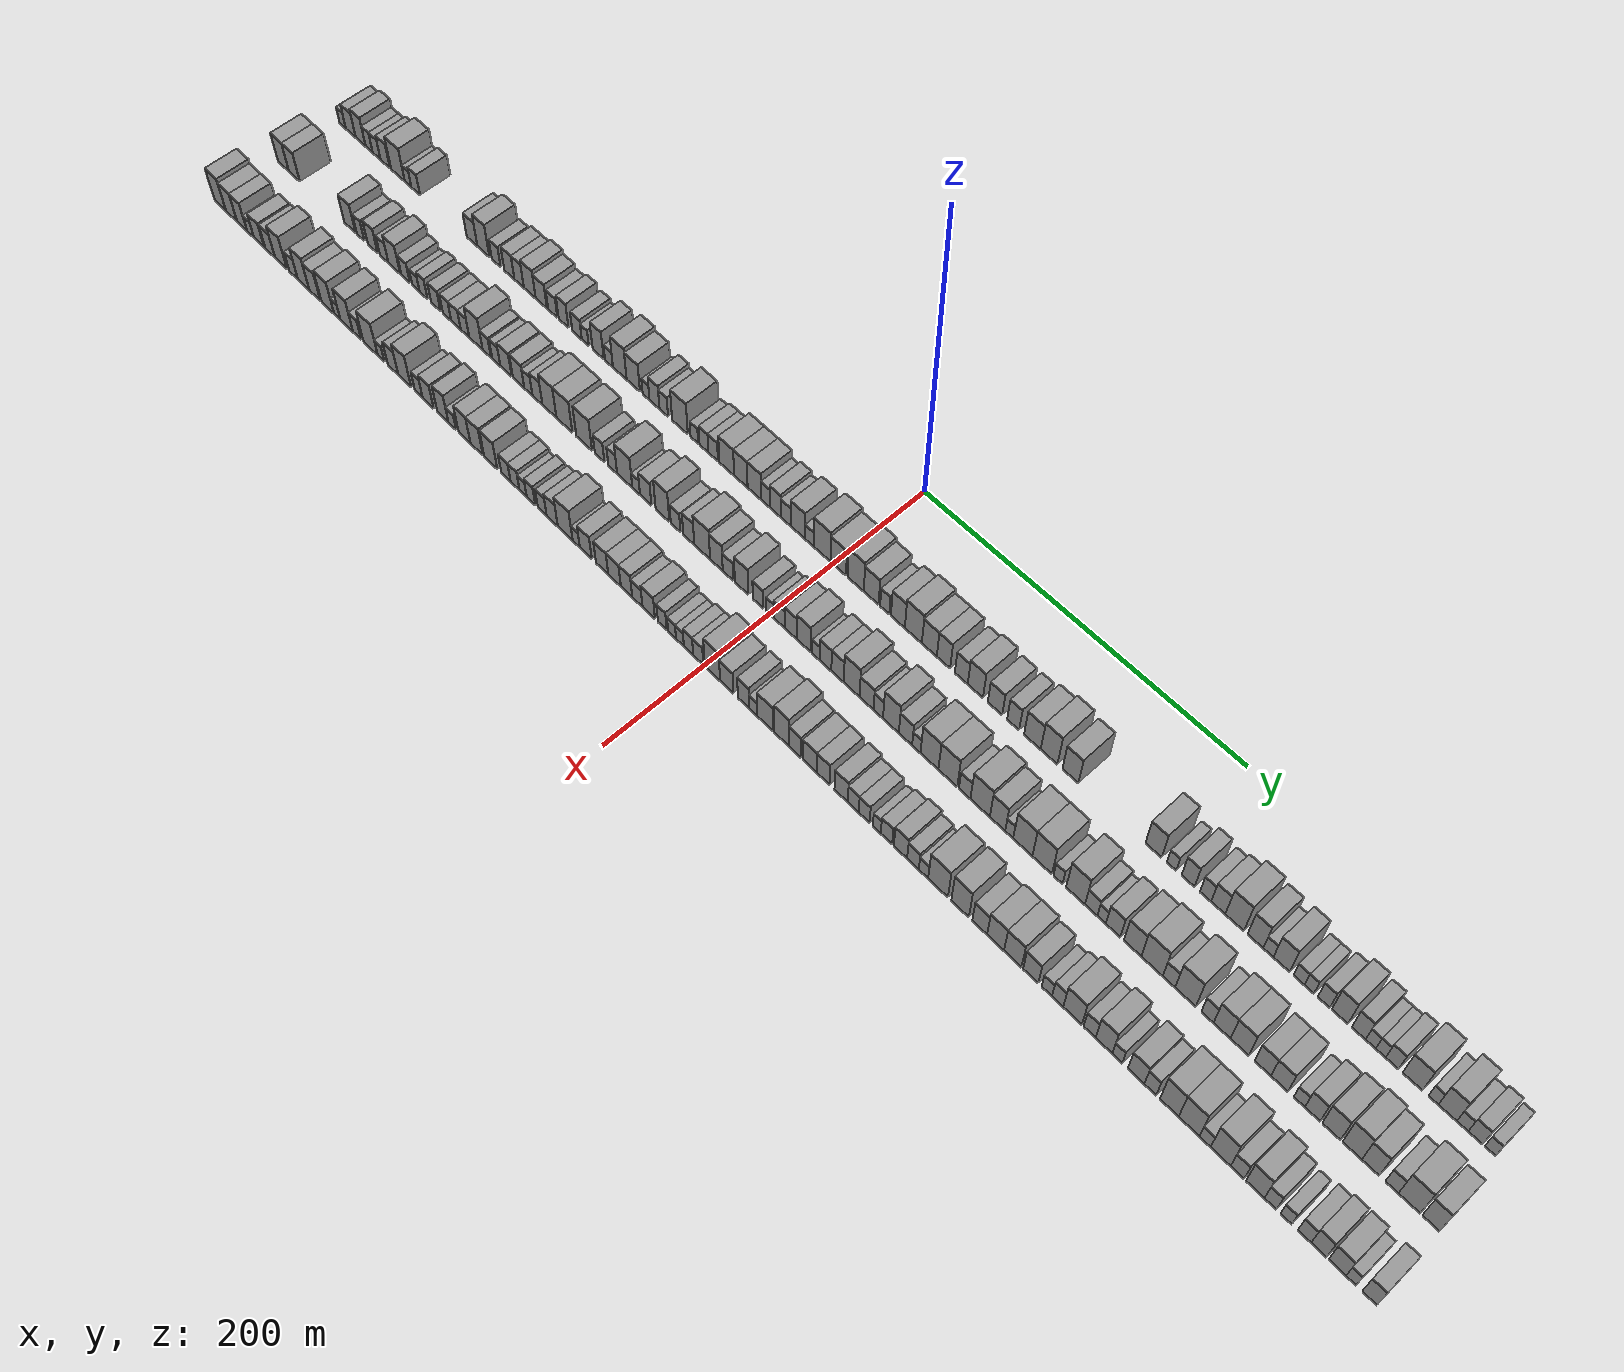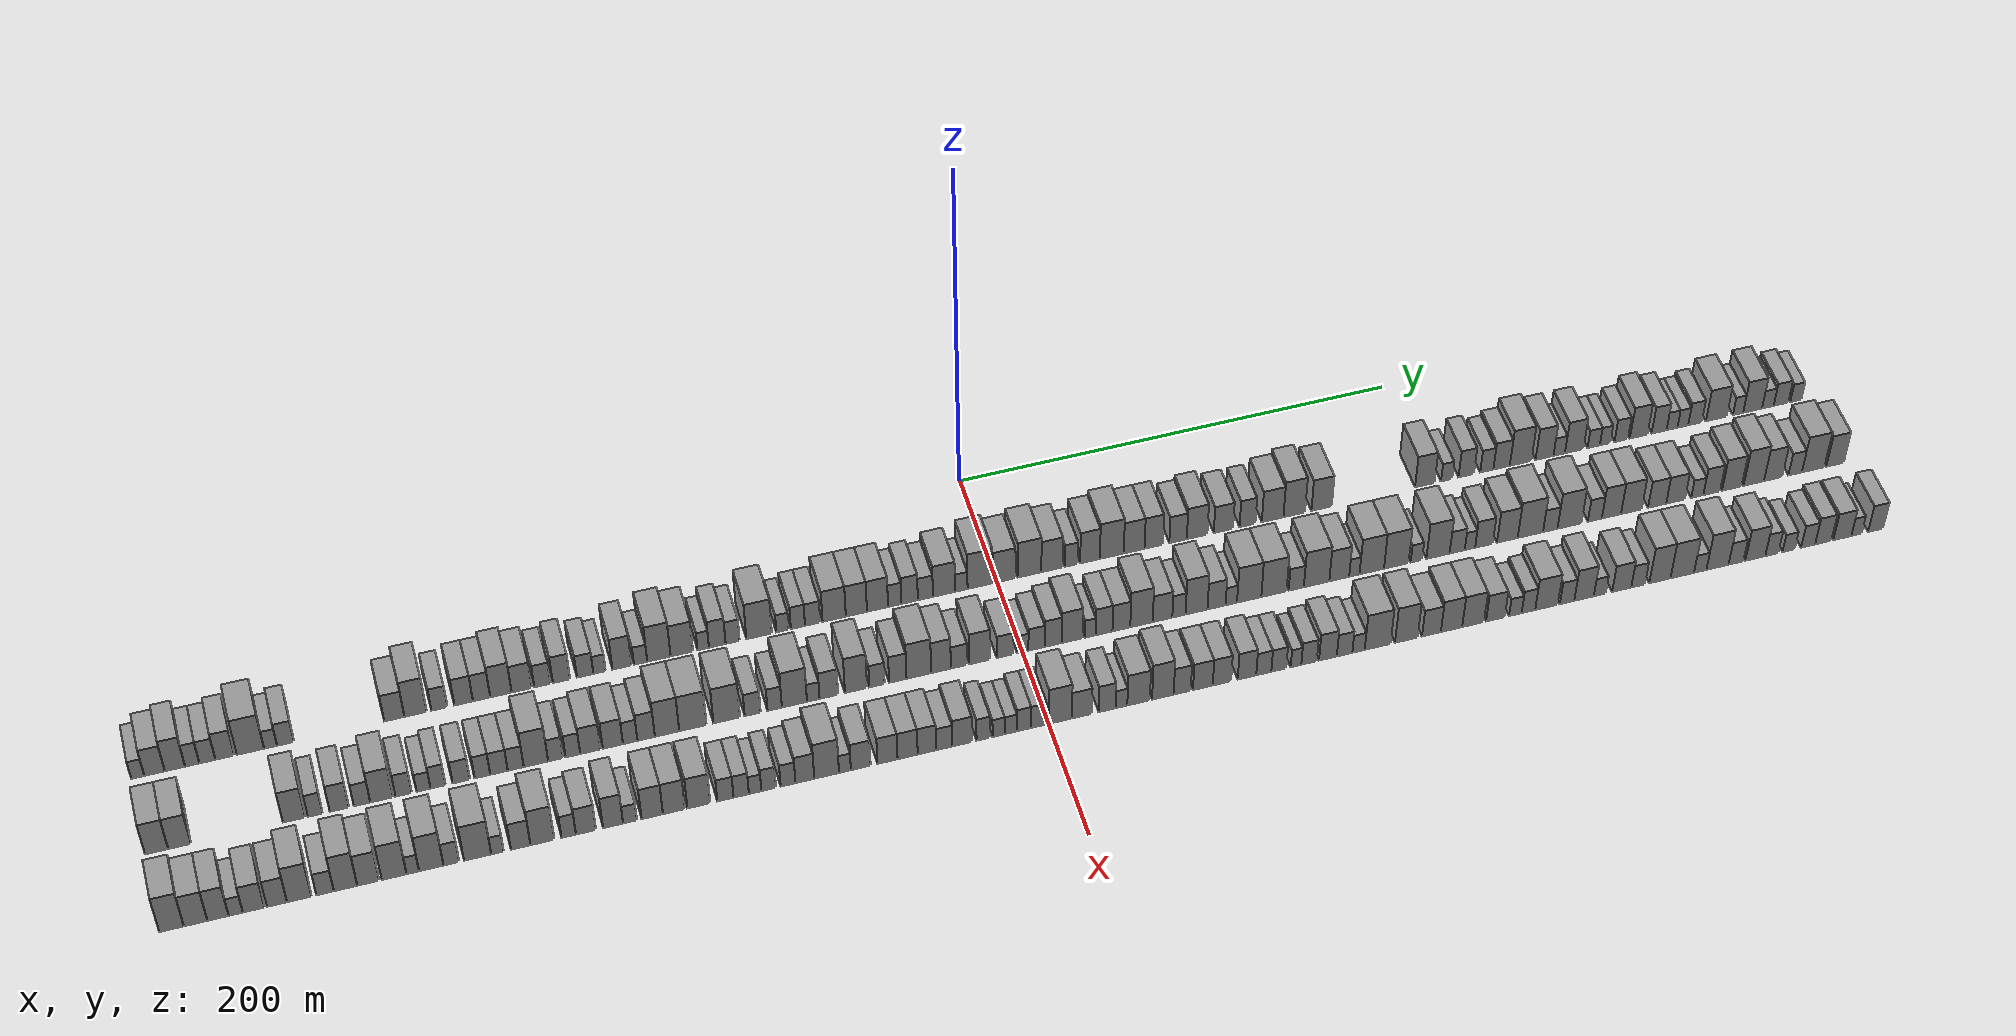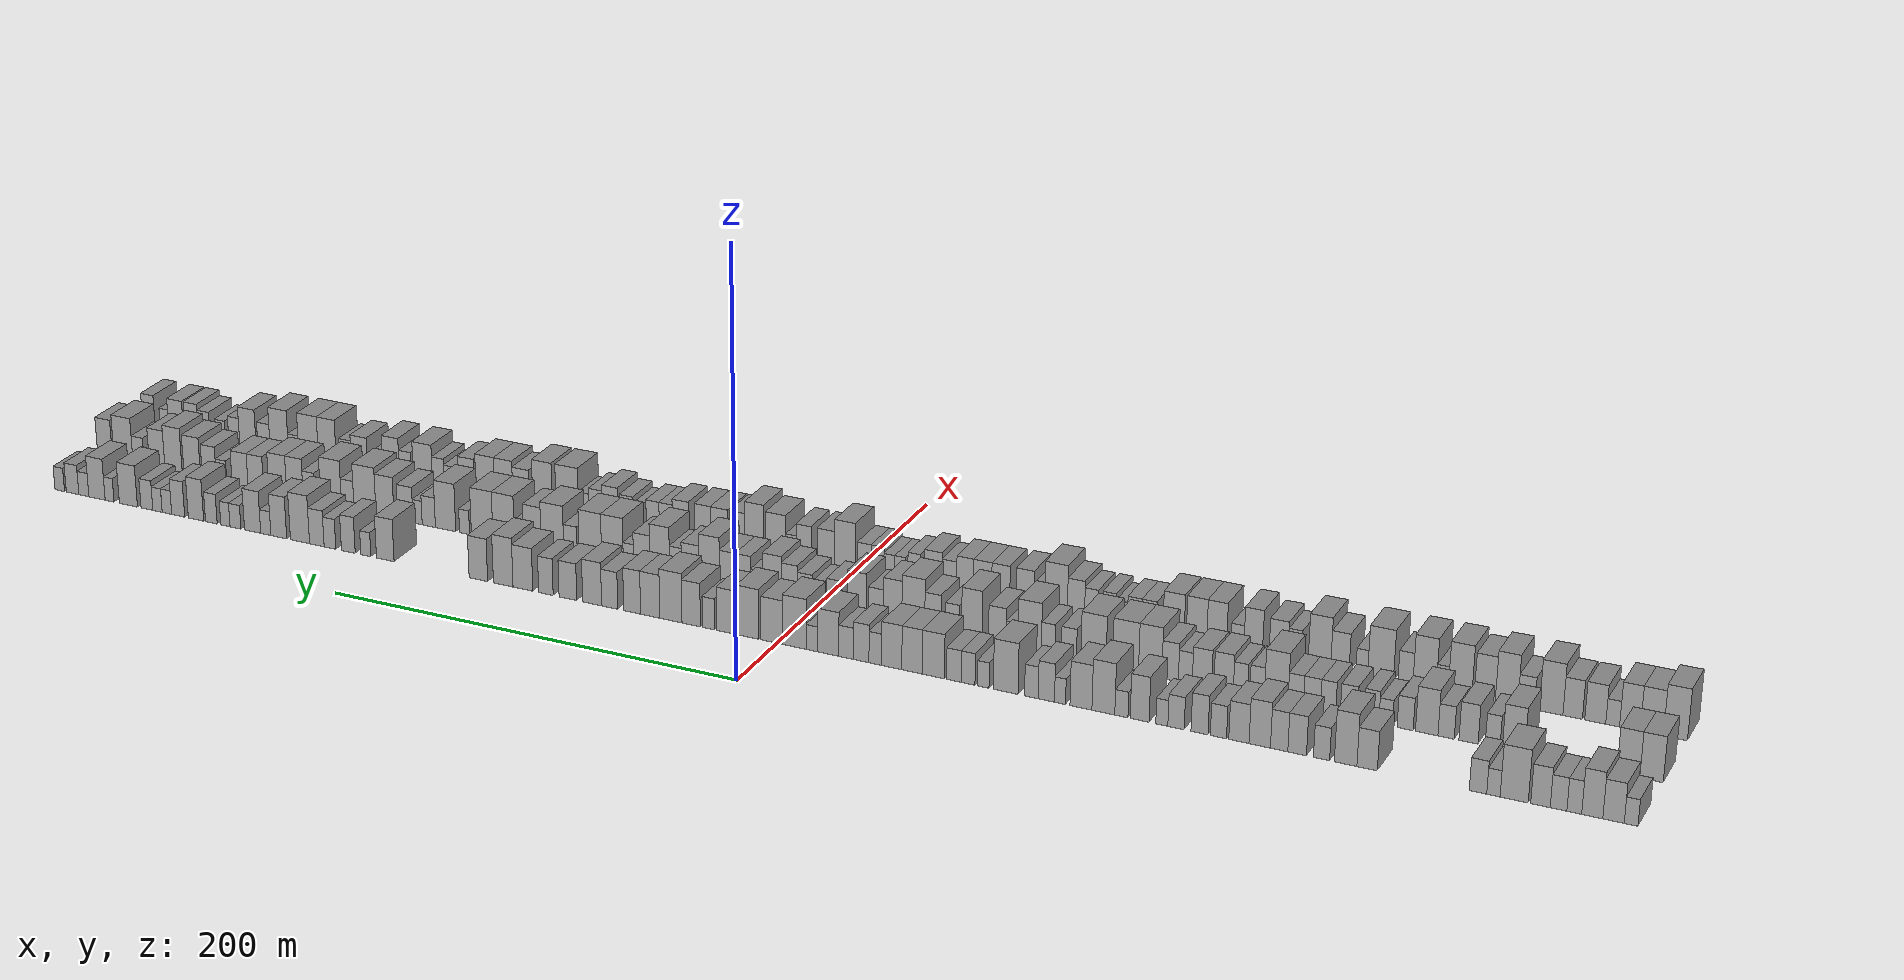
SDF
<sdf version="1.6">
 <world name="default">
  <scene>
   <sky><clouds><speed>12</speed></clouds></sky>
   <ambient>0.4 0.4 0.4 1</ambient>
   <background>0.7 0.7 0.7 1</background>
   <shadows>1</shadows>
  </scene>
  <gravity>0 0 -9.8066</gravity>
  <magnetic_field>6e-06 2.3e-05 -4.2e-05</magnetic_field>
  <physics default="0" name="default_physics" type="ode">
   <ode>
    <solver>
     <type>quick</type>
     <iters>10</iters>
     <sor>1.0</sor>
     <use_dynamic_moi_rescaling>0</use_dynamic_moi_rescaling>
    </solver>
    <constraints>
     <cfm>0</cfm>
     <erp>0.2</erp>
     <contact_max_correcting_vel>100</contact_max_correcting_vel>
     <contact_surface_layer>0.001</contact_surface_layer>
    </constraints>
   </ode>
   <max_step_size>0.004</max_step_size>
   <real_time_factor>1</real_time_factor>
   <real_time_update_rate>250</real_time_update_rate>
  </physics>
  <light name="sun" type="directional">
   <pose>0 0 10 0 0 0</pose>
   <diffuse>0.8 0.8 0.8 1</diffuse>
   <specular>0.2 0.2 0.2 1</specular>
   <attenuation>
    <range>1000</range>
    <constant>0.9</constant>
    <linear>0.01</linear>
    <quadratic>0.001</quadratic>
   </attenuation>
   <direction>-0.5 0.1 -0.9</direction>
  </light>
  <model name="building_1">
   <static>1</static>
   <pose>50.0000 -377.2303 0 0.000000 0.000000 0.000000</pose>
   <link name="link">
    <pose>0 0 6.00 0 0 0</pose>
    <collision name="collision"><geometry><box><size>20.0000 5.5395 12.0000</size></box></geometry></collision>
    <visual name="visual">
     <cast_shadows>0</cast_shadows>
     <geometry><box><size>20.0000 5.5395 12.0000</size></box></geometry>
     <material>
      <script>
       <uri>model://grey_wall/materials/scripts</uri>
       <uri>model://grey_wall/materials/textures</uri>
       <name>vrc/grey_wall</name>
      </script>
     </material>
    </visual>
   </link>
  </model>
  <model name="building_2">
   <static>1</static>
   <pose>50.0000 -370.1167 0 0.000000 0.000000 0.000000</pose>
   <link name="link">
    <pose>0 0 9.00 0 0 0</pose>
    <collision name="collision"><geometry><box><size>20.0000 8.6876 18.0000</size></box></geometry></collision>
    <visual name="visual">
     <cast_shadows>0</cast_shadows>
     <geometry><box><size>20.0000 8.6876 18.0000</size></box></geometry>
     <material>
      <script>
       <uri>model://grey_wall/materials/scripts</uri>
       <uri>model://grey_wall/materials/textures</uri>
       <name>vrc/grey_wall</name>
      </script>
     </material>
    </visual>
   </link>
  </model>
  <model name="building_3">
   <static>1</static>
   <pose>50.0000 -361.4806 0 0.000000 0.000000 0.000000</pose>
   <link name="link">
    <pose>0 0 10.50 0 0 0</pose>
    <collision name="collision"><geometry><box><size>20.0000 8.5846 21.0000</size></box></geometry></collision>
    <visual name="visual">
     <cast_shadows>0</cast_shadows>
     <geometry><box><size>20.0000 8.5846 21.0000</size></box></geometry>
     <material>
      <script>
       <uri>model://grey_wall/materials/scripts</uri>
       <uri>model://grey_wall/materials/textures</uri>
       <name>vrc/grey_wall</name>
      </script>
     </material>
    </visual>
   </link>
  </model>
  <model name="building_4">
   <static>1</static>
   <pose>50.0000 -354.1550 0 0.000000 0.000000 0.000000</pose>
   <link name="link">
    <pose>0 0 7.50 0 0 0</pose>
    <collision name="collision"><geometry><box><size>20.0000 6.0665 15.0000</size></box></geometry></collision>
    <visual name="visual">
     <cast_shadows>0</cast_shadows>
     <geometry><box><size>20.0000 6.0665 15.0000</size></box></geometry>
     <material>
      <script>
       <uri>model://grey_wall/materials/scripts</uri>
       <uri>model://grey_wall/materials/textures</uri>
       <name>vrc/grey_wall</name>
      </script>
     </material>
    </visual>
   </link>
  </model>
  <model name="building_5">
   <static>1</static>
   <pose>50.0000 -347.7063 0 0.000000 0.000000 0.000000</pose>
   <link name="link">
    <pose>0 0 7.50 0 0 0</pose>
    <collision name="collision"><geometry><box><size>20.0000 6.8309 15.0000</size></box></geometry></collision>
    <visual name="visual">
     <cast_shadows>0</cast_shadows>
     <geometry><box><size>20.0000 6.8309 15.0000</size></box></geometry>
     <material>
      <script>
       <uri>model://grey_wall/materials/scripts</uri>
       <uri>model://grey_wall/materials/textures</uri>
       <name>vrc/grey_wall</name>
      </script>
     </material>
    </visual>
   </link>
  </model>
  <model name="building_6">
   <static>1</static>
   <pose>50.0000 -340.2723 0 0.000000 0.000000 0.000000</pose>
   <link name="link">
    <pose>0 0 9.00 0 0 0</pose>
    <collision name="collision"><geometry><box><size>20.0000 8.0372 18.0000</size></box></geometry></collision>
    <visual name="visual">
     <cast_shadows>0</cast_shadows>
     <geometry><box><size>20.0000 8.0372 18.0000</size></box></geometry>
     <material>
      <script>
       <uri>model://grey_wall/materials/scripts</uri>
       <uri>model://grey_wall/materials/textures</uri>
       <name>vrc/grey_wall</name>
      </script>
     </material>
    </visual>
   </link>
  </model>
  <model name="building_7">
   <static>1</static>
   <pose>50.0000 -329.4300 0 0.000000 0.000000 0.000000</pose>
   <link name="link">
    <pose>0 0 12.00 0 0 0</pose>
    <collision name="collision"><geometry><box><size>20.0000 11.6474 24.0000</size></box></geometry></collision>
    <visual name="visual">
     <cast_shadows>0</cast_shadows>
     <geometry><box><size>20.0000 11.6474 24.0000</size></box></geometry>
     <material>
      <script>
       <uri>model://grey_wall/materials/scripts</uri>
       <uri>model://grey_wall/materials/textures</uri>
       <name>vrc/grey_wall</name>
      </script>
     </material>
    </visual>
   </link>
  </model>
  <model name="building_8">
   <static>1</static>
   <pose>50.0000 -320.8311 0 0.000000 0.000000 0.000000</pose>
   <link name="link">
    <pose>0 0 6.00 0 0 0</pose>
    <collision name="collision"><geometry><box><size>20.0000 5.5504 12.0000</size></box></geometry></collision>
    <visual name="visual">
     <cast_shadows>0</cast_shadows>
     <geometry><box><size>20.0000 5.5504 12.0000</size></box></geometry>
     <material>
      <script>
       <uri>model://grey_wall/materials/scripts</uri>
       <uri>model://grey_wall/materials/textures</uri>
       <name>vrc/grey_wall</name>
      </script>
     </material>
    </visual>
   </link>
  </model>
  <model name="building_9">
   <static>1</static>
   <pose>50.0000 -314.4221 0 0.000000 0.000000 0.000000</pose>
   <link name="link">
    <pose>0 0 7.50 0 0 0</pose>
    <collision name="collision"><geometry><box><size>20.0000 7.2676 15.0000</size></box></geometry></collision>
    <visual name="visual">
     <cast_shadows>0</cast_shadows>
     <geometry><box><size>20.0000 7.2676 15.0000</size></box></geometry>
     <material>
      <script>
       <uri>model://grey_wall/materials/scripts</uri>
       <uri>model://grey_wall/materials/textures</uri>
       <name>vrc/grey_wall</name>
      </script>
     </material>
    </visual>
   </link>
  </model>
  <model name="building_10">
   <static>1</static>
   <pose>50.0000 -267.6759 0 0.000000 0.000000 0.000000</pose>
   <link name="link">
    <pose>0 0 9.00 0 0 0</pose>
    <collision name="collision"><geometry><box><size>20.0000 8.7416 18.0000</size></box></geometry></collision>
    <visual name="visual">
     <cast_shadows>0</cast_shadows>
     <geometry><box><size>20.0000 8.7416 18.0000</size></box></geometry>
     <material>
      <script>
       <uri>model://grey_wall/materials/scripts</uri>
       <uri>model://grey_wall/materials/textures</uri>
       <name>vrc/grey_wall</name>
      </script>
     </material>
    </visual>
   </link>
  </model>
  <model name="building_11">
   <static>1</static>
   <pose>50.0000 -258.4627 0 0.000000 0.000000 0.000000</pose>
   <link name="link">
    <pose>0 0 12.00 0 0 0</pose>
    <collision name="collision"><geometry><box><size>20.0000 9.6846 24.0000</size></box></geometry></collision>
    <visual name="visual">
     <cast_shadows>0</cast_shadows>
     <geometry><box><size>20.0000 9.6846 24.0000</size></box></geometry>
     <material>
      <script>
       <uri>model://grey_wall/materials/scripts</uri>
       <uri>model://grey_wall/materials/textures</uri>
       <name>vrc/grey_wall</name>
      </script>
     </material>
    </visual>
   </link>
  </model>
  <model name="building_12">
   <static>1</static>
   <pose>50.0000 -248.1297 0 0.000000 0.000000 0.000000</pose>
   <link name="link">
    <pose>0 0 7.50 0 0 0</pose>
    <collision name="collision"><geometry><box><size>20.0000 6.9814 15.0000</size></box></geometry></collision>
    <visual name="visual">
     <cast_shadows>0</cast_shadows>
     <geometry><box><size>20.0000 6.9814 15.0000</size></box></geometry>
     <material>
      <script>
       <uri>model://grey_wall/materials/scripts</uri>
       <uri>model://grey_wall/materials/textures</uri>
       <name>vrc/grey_wall</name>
      </script>
     </material>
    </visual>
   </link>
  </model>
  <model name="building_13">
   <static>1</static>
   <pose>50.0000 -237.5989 0 0.000000 0.000000 0.000000</pose>
   <link name="link">
    <pose>0 0 9.00 0 0 0</pose>
    <collision name="collision"><geometry><box><size>20.0000 8.0801 18.0000</size></box></geometry></collision>
    <visual name="visual">
     <cast_shadows>0</cast_shadows>
     <geometry><box><size>20.0000 8.0801 18.0000</size></box></geometry>
     <material>
      <script>
       <uri>model://grey_wall/materials/scripts</uri>
       <uri>model://grey_wall/materials/textures</uri>
       <name>vrc/grey_wall</name>
      </script>
     </material>
    </visual>
   </link>
  </model>
  <model name="building_14">
   <static>1</static>
   <pose>50.0000 -229.7925 0 0.000000 0.000000 0.000000</pose>
   <link name="link">
    <pose>0 0 9.00 0 0 0</pose>
    <collision name="collision"><geometry><box><size>20.0000 7.5328 18.0000</size></box></geometry></collision>
    <visual name="visual">
     <cast_shadows>0</cast_shadows>
     <geometry><box><size>20.0000 7.5328 18.0000</size></box></geometry>
     <material>
      <script>
       <uri>model://grey_wall/materials/scripts</uri>
       <uri>model://grey_wall/materials/textures</uri>
       <name>vrc/grey_wall</name>
      </script>
     </material>
    </visual>
   </link>
  </model>
  <model name="building_15">
   <static>1</static>
   <pose>50.0000 -221.3531 0 0.000000 0.000000 0.000000</pose>
   <link name="link">
    <pose>0 0 10.50 0 0 0</pose>
    <collision name="collision"><geometry><box><size>20.0000 9.3460 21.0000</size></box></geometry></collision>
    <visual name="visual">
     <cast_shadows>0</cast_shadows>
     <geometry><box><size>20.0000 9.3460 21.0000</size></box></geometry>
     <material>
      <script>
       <uri>model://grey_wall/materials/scripts</uri>
       <uri>model://grey_wall/materials/textures</uri>
       <name>vrc/grey_wall</name>
      </script>
     </material>
    </visual>
   </link>
  </model>
  <model name="building_16">
   <static>1</static>
   <pose>50.0000 -212.2485 0 0.000000 0.000000 0.000000</pose>
   <link name="link">
    <pose>0 0 9.00 0 0 0</pose>
    <collision name="collision"><geometry><box><size>20.0000 8.8632 18.0000</size></box></geometry></collision>
    <visual name="visual">
     <cast_shadows>0</cast_shadows>
     <geometry><box><size>20.0000 8.8632 18.0000</size></box></geometry>
     <material>
      <script>
       <uri>model://grey_wall/materials/scripts</uri>
       <uri>model://grey_wall/materials/textures</uri>
       <name>vrc/grey_wall</name>
      </script>
     </material>
    </visual>
   </link>
  </model>
  <model name="building_17">
   <static>1</static>
   <pose>50.0000 -203.2530 0 0.000000 0.000000 0.000000</pose>
   <link name="link">
    <pose>0 0 7.50 0 0 0</pose>
    <collision name="collision"><geometry><box><size>20.0000 7.1278 15.0000</size></box></geometry></collision>
    <visual name="visual">
     <cast_shadows>0</cast_shadows>
     <geometry><box><size>20.0000 7.1278 15.0000</size></box></geometry>
     <material>
      <script>
       <uri>model://grey_wall/materials/scripts</uri>
       <uri>model://grey_wall/materials/textures</uri>
       <name>vrc/grey_wall</name>
      </script>
     </material>
    </visual>
   </link>
  </model>
  <model name="building_18">
   <static>1</static>
   <pose>50.0000 -194.9167 0 0.000000 0.000000 0.000000</pose>
   <link name="link">
    <pose>0 0 9.00 0 0 0</pose>
    <collision name="collision"><geometry><box><size>20.0000 7.5448 18.0000</size></box></geometry></collision>
    <visual name="visual">
     <cast_shadows>0</cast_shadows>
     <geometry><box><size>20.0000 7.5448 18.0000</size></box></geometry>
     <material>
      <script>
       <uri>model://grey_wall/materials/scripts</uri>
       <uri>model://grey_wall/materials/textures</uri>
       <name>vrc/grey_wall</name>
      </script>
     </material>
    </visual>
   </link>
  </model>
  <model name="building_19">
   <static>1</static>
   <pose>50.0000 -184.5215 0 0.000000 0.000000 0.000000</pose>
   <link name="link">
    <pose>0 0 7.50 0 0 0</pose>
    <collision name="collision"><geometry><box><size>20.0000 7.2455 15.0000</size></box></geometry></collision>
    <visual name="visual">
     <cast_shadows>0</cast_shadows>
     <geometry><box><size>20.0000 7.2455 15.0000</size></box></geometry>
     <material>
      <script>
       <uri>model://grey_wall/materials/scripts</uri>
       <uri>model://grey_wall/materials/textures</uri>
       <name>vrc/grey_wall</name>
      </script>
     </material>
    </visual>
   </link>
  </model>
  <model name="building_20">
   <static>1</static>
   <pose>50.0000 -178.2118 0 0.000000 0.000000 0.000000</pose>
   <link name="link">
    <pose>0 0 6.00 0 0 0</pose>
    <collision name="collision"><geometry><box><size>20.0000 5.3739 12.0000</size></box></geometry></collision>
    <visual name="visual">
     <cast_shadows>0</cast_shadows>
     <geometry><box><size>20.0000 5.3739 12.0000</size></box></geometry>
     <material>
      <script>
       <uri>model://grey_wall/materials/scripts</uri>
       <uri>model://grey_wall/materials/textures</uri>
       <name>vrc/grey_wall</name>
      </script>
     </material>
    </visual>
   </link>
  </model>
  <model name="building_21">
   <static>1</static>
   <pose>50.0000 -168.3030 0 0.000000 0.000000 0.000000</pose>
   <link name="link">
    <pose>0 0 10.50 0 0 0</pose>
    <collision name="collision"><geometry><box><size>20.0000 8.4436 21.0000</size></box></geometry></collision>
    <visual name="visual">
     <cast_shadows>0</cast_shadows>
     <geometry><box><size>20.0000 8.4436 21.0000</size></box></geometry>
     <material>
      <script>
       <uri>model://grey_wall/materials/scripts</uri>
       <uri>model://grey_wall/materials/textures</uri>
       <name>vrc/grey_wall</name>
      </script>
     </material>
    </visual>
   </link>
  </model>
  <model name="building_22">
   <static>1</static>
   <pose>50.0000 -160.1212 0 0.000000 0.000000 0.000000</pose>
   <link name="link">
    <pose>0 0 6.00 0 0 0</pose>
    <collision name="collision"><geometry><box><size>20.0000 5.9200 12.0000</size></box></geometry></collision>
    <visual name="visual">
     <cast_shadows>0</cast_shadows>
     <geometry><box><size>20.0000 5.9200 12.0000</size></box></geometry>
     <material>
      <script>
       <uri>model://grey_wall/materials/scripts</uri>
       <uri>model://grey_wall/materials/textures</uri>
       <name>vrc/grey_wall</name>
      </script>
     </material>
    </visual>
   </link>
  </model>
  <model name="building_23">
   <static>1</static>
   <pose>50.0000 -152.0052 0 0.000000 0.000000 0.000000</pose>
   <link name="link">
    <pose>0 0 12.00 0 0 0</pose>
    <collision name="collision"><geometry><box><size>20.0000 10.3118 24.0000</size></box></geometry></collision>
    <visual name="visual">
     <cast_shadows>0</cast_shadows>
     <geometry><box><size>20.0000 10.3118 24.0000</size></box></geometry>
     <material>
      <script>
       <uri>model://grey_wall/materials/scripts</uri>
       <uri>model://grey_wall/materials/textures</uri>
       <name>vrc/grey_wall</name>
      </script>
     </material>
    </visual>
   </link>
  </model>
  <model name="building_24">
   <static>1</static>
   <pose>50.0000 -141.8778 0 0.000000 0.000000 0.000000</pose>
   <link name="link">
    <pose>0 0 10.50 0 0 0</pose>
    <collision name="collision"><geometry><box><size>20.0000 9.9431 21.0000</size></box></geometry></collision>
    <visual name="visual">
     <cast_shadows>0</cast_shadows>
     <geometry><box><size>20.0000 9.9431 21.0000</size></box></geometry>
     <material>
      <script>
       <uri>model://grey_wall/materials/scripts</uri>
       <uri>model://grey_wall/materials/textures</uri>
       <name>vrc/grey_wall</name>
      </script>
     </material>
    </visual>
   </link>
  </model>
  <model name="building_25">
   <static>1</static>
   <pose>50.0000 -132.3849 0 0.000000 0.000000 0.000000</pose>
   <link name="link">
    <pose>0 0 6.00 0 0 0</pose>
    <collision name="collision"><geometry><box><size>20.0000 5.0427 12.0000</size></box></geometry></collision>
    <visual name="visual">
     <cast_shadows>0</cast_shadows>
     <geometry><box><size>20.0000 5.0427 12.0000</size></box></geometry>
     <material>
      <script>
       <uri>model://grey_wall/materials/scripts</uri>
       <uri>model://grey_wall/materials/textures</uri>
       <name>vrc/grey_wall</name>
      </script>
     </material>
    </visual>
   </link>
  </model>
  <model name="building_26">
   <static>1</static>
   <pose>50.0000 -126.1405 0 0.000000 0.000000 0.000000</pose>
   <link name="link">
    <pose>0 0 9.00 0 0 0</pose>
    <collision name="collision"><geometry><box><size>20.0000 7.4460 18.0000</size></box></geometry></collision>
    <visual name="visual">
     <cast_shadows>0</cast_shadows>
     <geometry><box><size>20.0000 7.4460 18.0000</size></box></geometry>
     <material>
      <script>
       <uri>model://grey_wall/materials/scripts</uri>
       <uri>model://grey_wall/materials/textures</uri>
       <name>vrc/grey_wall</name>
      </script>
     </material>
    </visual>
   </link>
  </model>
  <model name="building_27">
   <static>1</static>
   <pose>50.0000 -119.2987 0 0.000000 0.000000 0.000000</pose>
   <link name="link">
    <pose>0 0 7.50 0 0 0</pose>
    <collision name="collision"><geometry><box><size>20.0000 6.2375 15.0000</size></box></geometry></collision>
    <visual name="visual">
     <cast_shadows>0</cast_shadows>
     <geometry><box><size>20.0000 6.2375 15.0000</size></box></geometry>
     <material>
      <script>
       <uri>model://grey_wall/materials/scripts</uri>
       <uri>model://grey_wall/materials/textures</uri>
       <name>vrc/grey_wall</name>
      </script>
     </material>
    </visual>
   </link>
  </model>
  <model name="building_28">
   <static>1</static>
   <pose>50.0000 -107.4971 0 0.000000 0.000000 0.000000</pose>
   <link name="link">
    <pose>0 0 12.00 0 0 0</pose>
    <collision name="collision"><geometry><box><size>20.0000 11.3657 24.0000</size></box></geometry></collision>
    <visual name="visual">
     <cast_shadows>0</cast_shadows>
     <geometry><box><size>20.0000 11.3657 24.0000</size></box></geometry>
     <material>
      <script>
       <uri>model://grey_wall/materials/scripts</uri>
       <uri>model://grey_wall/materials/textures</uri>
       <name>vrc/grey_wall</name>
      </script>
     </material>
    </visual>
   </link>
  </model>
  <model name="building_29">
   <static>1</static>
   <pose>50.0000 -97.0648 0 0.000000 0.000000 0.000000</pose>
   <link name="link">
    <pose>0 0 6.00 0 0 0</pose>
    <collision name="collision"><geometry><box><size>20.0000 5.4989 12.0000</size></box></geometry></collision>
    <visual name="visual">
     <cast_shadows>0</cast_shadows>
     <geometry><box><size>20.0000 5.4989 12.0000</size></box></geometry>
     <material>
      <script>
       <uri>model://grey_wall/materials/scripts</uri>
       <uri>model://grey_wall/materials/textures</uri>
       <name>vrc/grey_wall</name>
      </script>
     </material>
    </visual>
   </link>
  </model>
  <model name="building_30">
   <static>1</static>
   <pose>50.0000 -90.1429 0 0.000000 0.000000 0.000000</pose>
   <link name="link">
    <pose>0 0 7.50 0 0 0</pose>
    <collision name="collision"><geometry><box><size>20.0000 6.3448 15.0000</size></box></geometry></collision>
    <visual name="visual">
     <cast_shadows>0</cast_shadows>
     <geometry><box><size>20.0000 6.3448 15.0000</size></box></geometry>
     <material>
      <script>
       <uri>model://grey_wall/materials/scripts</uri>
       <uri>model://grey_wall/materials/textures</uri>
       <name>vrc/grey_wall</name>
      </script>
     </material>
    </visual>
   </link>
  </model>
  <model name="building_31">
   <static>1</static>
   <pose>50.0000 -83.5519 0 0.000000 0.000000 0.000000</pose>
   <link name="link">
    <pose>0 0 7.50 0 0 0</pose>
    <collision name="collision"><geometry><box><size>20.0000 6.8373 15.0000</size></box></geometry></collision>
    <visual name="visual">
     <cast_shadows>0</cast_shadows>
     <geometry><box><size>20.0000 6.8373 15.0000</size></box></geometry>
     <material>
      <script>
       <uri>model://grey_wall/materials/scripts</uri>
       <uri>model://grey_wall/materials/textures</uri>
       <name>vrc/grey_wall</name>
      </script>
     </material>
    </visual>
   </link>
  </model>
  <model name="building_32">
   <static>1</static>
   <pose>50.0000 -73.8972 0 0.000000 0.000000 0.000000</pose>
   <link name="link">
    <pose>0 0 10.50 0 0 0</pose>
    <collision name="collision"><geometry><box><size>20.0000 10.4721 21.0000</size></box></geometry></collision>
    <visual name="visual">
     <cast_shadows>0</cast_shadows>
     <geometry><box><size>20.0000 10.4721 21.0000</size></box></geometry>
     <material>
      <script>
       <uri>model://grey_wall/materials/scripts</uri>
       <uri>model://grey_wall/materials/textures</uri>
       <name>vrc/grey_wall</name>
      </script>
     </material>
    </visual>
   </link>
  </model>
  <model name="building_33">
   <static>1</static>
   <pose>50.0000 -63.8988 0 0.000000 0.000000 0.000000</pose>
   <link name="link">
    <pose>0 0 10.50 0 0 0</pose>
    <collision name="collision"><geometry><box><size>20.0000 9.5246 21.0000</size></box></geometry></collision>
    <visual name="visual">
     <cast_shadows>0</cast_shadows>
     <geometry><box><size>20.0000 9.5246 21.0000</size></box></geometry>
     <material>
      <script>
       <uri>model://grey_wall/materials/scripts</uri>
       <uri>model://grey_wall/materials/textures</uri>
       <name>vrc/grey_wall</name>
      </script>
     </material>
    </visual>
   </link>
  </model>
  <model name="building_34">
   <static>1</static>
   <pose>50.0000 -54.3746 0 0.000000 0.000000 0.000000</pose>
   <link name="link">
    <pose>0 0 10.50 0 0 0</pose>
    <collision name="collision"><geometry><box><size>20.0000 9.5240 21.0000</size></box></geometry></collision>
    <visual name="visual">
     <cast_shadows>0</cast_shadows>
     <geometry><box><size>20.0000 9.5240 21.0000</size></box></geometry>
     <material>
      <script>
       <uri>model://grey_wall/materials/scripts</uri>
       <uri>model://grey_wall/materials/textures</uri>
       <name>vrc/grey_wall</name>
      </script>
     </material>
    </visual>
   </link>
  </model>
  <model name="building_35">
   <static>1</static>
   <pose>50.0000 -46.6111 0 0.000000 0.000000 0.000000</pose>
   <link name="link">
    <pose>0 0 7.50 0 0 0</pose>
    <collision name="collision"><geometry><box><size>20.0000 6.0030 15.0000</size></box></geometry></collision>
    <visual name="visual">
     <cast_shadows>0</cast_shadows>
     <geometry><box><size>20.0000 6.0030 15.0000</size></box></geometry>
     <material>
      <script>
       <uri>model://grey_wall/materials/scripts</uri>
       <uri>model://grey_wall/materials/textures</uri>
       <name>vrc/grey_wall</name>
      </script>
     </material>
    </visual>
   </link>
  </model>
  <model name="building_36">
   <static>1</static>
   <pose>50.0000 -39.8862 0 0.000000 0.000000 0.000000</pose>
   <link name="link">
    <pose>0 0 9.00 0 0 0</pose>
    <collision name="collision"><geometry><box><size>20.0000 7.4467 18.0000</size></box></geometry></collision>
    <visual name="visual">
     <cast_shadows>0</cast_shadows>
     <geometry><box><size>20.0000 7.4467 18.0000</size></box></geometry>
     <material>
      <script>
       <uri>model://grey_wall/materials/scripts</uri>
       <uri>model://grey_wall/materials/textures</uri>
       <name>vrc/grey_wall</name>
      </script>
     </material>
    </visual>
   </link>
  </model>
  <model name="building_37">
   <static>1</static>
   <pose>50.0000 -32.7455 0 0.000000 0.000000 0.000000</pose>
   <link name="link">
    <pose>0 0 7.50 0 0 0</pose>
    <collision name="collision"><geometry><box><size>20.0000 6.8346 15.0000</size></box></geometry></collision>
    <visual name="visual">
     <cast_shadows>0</cast_shadows>
     <geometry><box><size>20.0000 6.8346 15.0000</size></box></geometry>
     <material>
      <script>
       <uri>model://grey_wall/materials/scripts</uri>
       <uri>model://grey_wall/materials/textures</uri>
       <name>vrc/grey_wall</name>
      </script>
     </material>
    </visual>
   </link>
  </model>
  <model name="building_38">
   <static>1</static>
   <pose>50.0000 -24.3116 0 0.000000 0.000000 0.000000</pose>
   <link name="link">
    <pose>0 0 10.50 0 0 0</pose>
    <collision name="collision"><geometry><box><size>20.0000 10.0333 21.0000</size></box></geometry></collision>
    <visual name="visual">
     <cast_shadows>0</cast_shadows>
     <geometry><box><size>20.0000 10.0333 21.0000</size></box></geometry>
     <material>
      <script>
       <uri>model://grey_wall/materials/scripts</uri>
       <uri>model://grey_wall/materials/textures</uri>
       <name>vrc/grey_wall</name>
      </script>
     </material>
    </visual>
   </link>
  </model>
  <model name="building_39">
   <static>1</static>
   <pose>50.0000 -16.4530 0 0.000000 0.000000 0.000000</pose>
   <link name="link">
    <pose>0 0 6.00 0 0 0</pose>
    <collision name="collision"><geometry><box><size>20.0000 5.6837 12.0000</size></box></geometry></collision>
    <visual name="visual">
     <cast_shadows>0</cast_shadows>
     <geometry><box><size>20.0000 5.6837 12.0000</size></box></geometry>
     <material>
      <script>
       <uri>model://grey_wall/materials/scripts</uri>
       <uri>model://grey_wall/materials/textures</uri>
       <name>vrc/grey_wall</name>
      </script>
     </material>
    </visual>
   </link>
  </model>
  <model name="building_40">
   <static>1</static>
   <pose>50.0000 -7.8787 0 0.000000 0.000000 0.000000</pose>
   <link name="link">
    <pose>0 0 12.00 0 0 0</pose>
    <collision name="collision"><geometry><box><size>20.0000 11.4650 24.0000</size></box></geometry></collision>
    <visual name="visual">
     <cast_shadows>0</cast_shadows>
     <geometry><box><size>20.0000 11.4650 24.0000</size></box></geometry>
     <material>
      <script>
       <uri>model://grey_wall/materials/scripts</uri>
       <uri>model://grey_wall/materials/textures</uri>
       <name>vrc/grey_wall</name>
      </script>
     </material>
    </visual>
   </link>
  </model>
  <model name="building_41">
   <static>1</static>
   <pose>50.0000 3.0513 0 0.000000 0.000000 0.000000</pose>
   <link name="link">
    <pose>0 0 10.50 0 0 0</pose>
    <collision name="collision"><geometry><box><size>20.0000 10.3950 21.0000</size></box></geometry></collision>
    <visual name="visual">
     <cast_shadows>0</cast_shadows>
     <geometry><box><size>20.0000 10.3950 21.0000</size></box></geometry>
     <material>
      <script>
       <uri>model://grey_wall/materials/scripts</uri>
       <uri>model://grey_wall/materials/textures</uri>
       <name>vrc/grey_wall</name>
      </script>
     </material>
    </visual>
   </link>
  </model>
  <model name="building_42">
   <static>1</static>
   <pose>50.0000 14.6597 0 0.000000 0.000000 0.000000</pose>
   <link name="link">
    <pose>0 0 12.00 0 0 0</pose>
    <collision name="collision"><geometry><box><size>20.0000 10.8217 24.0000</size></box></geometry></collision>
    <visual name="visual">
     <cast_shadows>0</cast_shadows>
     <geometry><box><size>20.0000 10.8217 24.0000</size></box></geometry>
     <material>
      <script>
       <uri>model://grey_wall/materials/scripts</uri>
       <uri>model://grey_wall/materials/textures</uri>
       <name>vrc/grey_wall</name>
      </script>
     </material>
    </visual>
   </link>
  </model>
  <model name="building_43">
   <static>1</static>
   <pose>50.0000 24.9579 0 0.000000 0.000000 0.000000</pose>
   <link name="link">
    <pose>0 0 10.50 0 0 0</pose>
    <collision name="collision"><geometry><box><size>20.0000 9.7747 21.0000</size></box></geometry></collision>
    <visual name="visual">
     <cast_shadows>0</cast_shadows>
     <geometry><box><size>20.0000 9.7747 21.0000</size></box></geometry>
     <material>
      <script>
       <uri>model://grey_wall/materials/scripts</uri>
       <uri>model://grey_wall/materials/textures</uri>
       <name>vrc/grey_wall</name>
      </script>
     </material>
    </visual>
   </link>
  </model>
  <model name="building_44">
   <static>1</static>
   <pose>50.0000 33.8572 0 0.000000 0.000000 0.000000</pose>
   <link name="link">
    <pose>0 0 7.50 0 0 0</pose>
    <collision name="collision"><geometry><box><size>20.0000 6.0239 15.0000</size></box></geometry></collision>
    <visual name="visual">
     <cast_shadows>0</cast_shadows>
     <geometry><box><size>20.0000 6.0239 15.0000</size></box></geometry>
     <material>
      <script>
       <uri>model://grey_wall/materials/scripts</uri>
       <uri>model://grey_wall/materials/textures</uri>
       <name>vrc/grey_wall</name>
      </script>
     </material>
    </visual>
   </link>
  </model>
  <model name="building_45">
   <static>1</static>
   <pose>50.0000 42.4063 0 0.000000 0.000000 0.000000</pose>
   <link name="link">
    <pose>0 0 10.50 0 0 0</pose>
    <collision name="collision"><geometry><box><size>20.0000 9.0743 21.0000</size></box></geometry></collision>
    <visual name="visual">
     <cast_shadows>0</cast_shadows>
     <geometry><box><size>20.0000 9.0743 21.0000</size></box></geometry>
     <material>
      <script>
       <uri>model://grey_wall/materials/scripts</uri>
       <uri>model://grey_wall/materials/textures</uri>
       <name>vrc/grey_wall</name>
      </script>
     </material>
    </visual>
   </link>
  </model>
  <model name="building_46">
   <static>1</static>
   <pose>50.0000 52.4457 0 0.000000 0.000000 0.000000</pose>
   <link name="link">
    <pose>0 0 12.00 0 0 0</pose>
    <collision name="collision"><geometry><box><size>20.0000 11.0043 24.0000</size></box></geometry></collision>
    <visual name="visual">
     <cast_shadows>0</cast_shadows>
     <geometry><box><size>20.0000 11.0043 24.0000</size></box></geometry>
     <material>
      <script>
       <uri>model://grey_wall/materials/scripts</uri>
       <uri>model://grey_wall/materials/textures</uri>
       <name>vrc/grey_wall</name>
      </script>
     </material>
    </visual>
   </link>
  </model>
  <model name="building_47">
   <static>1</static>
   <pose>50.0000 62.7389 0 0.000000 0.000000 0.000000</pose>
   <link name="link">
    <pose>0 0 10.50 0 0 0</pose>
    <collision name="collision"><geometry><box><size>20.0000 9.5821 21.0000</size></box></geometry></collision>
    <visual name="visual">
     <cast_shadows>0</cast_shadows>
     <geometry><box><size>20.0000 9.5821 21.0000</size></box></geometry>
     <material>
      <script>
       <uri>model://grey_wall/materials/scripts</uri>
       <uri>model://grey_wall/materials/textures</uri>
       <name>vrc/grey_wall</name>
      </script>
     </material>
    </visual>
   </link>
  </model>
  <model name="building_48">
   <static>1</static>
   <pose>50.0000 71.7521 0 0.000000 0.000000 0.000000</pose>
   <link name="link">
    <pose>0 0 10.50 0 0 0</pose>
    <collision name="collision"><geometry><box><size>20.0000 8.4444 21.0000</size></box></geometry></collision>
    <visual name="visual">
     <cast_shadows>0</cast_shadows>
     <geometry><box><size>20.0000 8.4444 21.0000</size></box></geometry>
     <material>
      <script>
       <uri>model://grey_wall/materials/scripts</uri>
       <uri>model://grey_wall/materials/textures</uri>
       <name>vrc/grey_wall</name>
      </script>
     </material>
    </visual>
   </link>
  </model>
  <model name="building_49">
   <static>1</static>
   <pose>50.0000 83.0258 0 0.000000 0.000000 0.000000</pose>
   <link name="link">
    <pose>0 0 9.00 0 0 0</pose>
    <collision name="collision"><geometry><box><size>20.0000 8.1031 18.0000</size></box></geometry></collision>
    <visual name="visual">
     <cast_shadows>0</cast_shadows>
     <geometry><box><size>20.0000 8.1031 18.0000</size></box></geometry>
     <material>
      <script>
       <uri>model://grey_wall/materials/scripts</uri>
       <uri>model://grey_wall/materials/textures</uri>
       <name>vrc/grey_wall</name>
      </script>
     </material>
    </visual>
   </link>
  </model>
  <model name="building_50">
   <static>1</static>
   <pose>50.0000 91.8477 0 0.000000 0.000000 0.000000</pose>
   <link name="link">
    <pose>0 0 10.50 0 0 0</pose>
    <collision name="collision"><geometry><box><size>20.0000 9.5407 21.0000</size></box></geometry></collision>
    <visual name="visual">
     <cast_shadows>0</cast_shadows>
     <geometry><box><size>20.0000 9.5407 21.0000</size></box></geometry>
     <material>
      <script>
       <uri>model://grey_wall/materials/scripts</uri>
       <uri>model://grey_wall/materials/textures</uri>
       <name>vrc/grey_wall</name>
      </script>
     </material>
    </visual>
   </link>
  </model>
  <model name="building_51">
   <static>1</static>
   <pose>50.0000 104.1071 0 0.000000 0.000000 0.000000</pose>
   <link name="link">
    <pose>0 0 9.00 0 0 0</pose>
    <collision name="collision"><geometry><box><size>20.0000 8.9781 18.0000</size></box></geometry></collision>
    <visual name="visual">
     <cast_shadows>0</cast_shadows>
     <geometry><box><size>20.0000 8.9781 18.0000</size></box></geometry>
     <material>
      <script>
       <uri>model://grey_wall/materials/scripts</uri>
       <uri>model://grey_wall/materials/textures</uri>
       <name>vrc/grey_wall</name>
      </script>
     </material>
    </visual>
   </link>
  </model>
  <model name="building_52">
   <static>1</static>
   <pose>50.0000 115.2909 0 0.000000 0.000000 0.000000</pose>
   <link name="link">
    <pose>0 0 9.00 0 0 0</pose>
    <collision name="collision"><geometry><box><size>20.0000 7.3895 18.0000</size></box></geometry></collision>
    <visual name="visual">
     <cast_shadows>0</cast_shadows>
     <geometry><box><size>20.0000 7.3895 18.0000</size></box></geometry>
     <material>
      <script>
       <uri>model://grey_wall/materials/scripts</uri>
       <uri>model://grey_wall/materials/textures</uri>
       <name>vrc/grey_wall</name>
      </script>
     </material>
    </visual>
   </link>
  </model>
  <model name="building_53">
   <static>1</static>
   <pose>50.0000 127.0542 0 0.000000 0.000000 0.000000</pose>
   <link name="link">
    <pose>0 0 10.50 0 0 0</pose>
    <collision name="collision"><geometry><box><size>20.0000 10.1372 21.0000</size></box></geometry></collision>
    <visual name="visual">
     <cast_shadows>0</cast_shadows>
     <geometry><box><size>20.0000 10.1372 21.0000</size></box></geometry>
     <material>
      <script>
       <uri>model://grey_wall/materials/scripts</uri>
       <uri>model://grey_wall/materials/textures</uri>
       <name>vrc/grey_wall</name>
      </script>
     </material>
    </visual>
   </link>
  </model>
  <model name="building_54">
   <static>1</static>
   <pose>50.0000 137.1678 0 0.000000 0.000000 0.000000</pose>
   <link name="link">
    <pose>0 0 12.00 0 0 0</pose>
    <collision name="collision"><geometry><box><size>20.0000 10.0899 24.0000</size></box></geometry></collision>
    <visual name="visual">
     <cast_shadows>0</cast_shadows>
     <geometry><box><size>20.0000 10.0899 24.0000</size></box></geometry>
     <material>
      <script>
       <uri>model://grey_wall/materials/scripts</uri>
       <uri>model://grey_wall/materials/textures</uri>
       <name>vrc/grey_wall</name>
      </script>
     </material>
    </visual>
   </link>
  </model>
  <model name="building_55">
   <static>1</static>
   <pose>50.0000 150.0055 0 0.000000 0.000000 0.000000</pose>
   <link name="link">
    <pose>0 0 10.50 0 0 0</pose>
    <collision name="collision"><geometry><box><size>20.0000 9.5855 21.0000</size></box></geometry></collision>
    <visual name="visual">
     <cast_shadows>0</cast_shadows>
     <geometry><box><size>20.0000 9.5855 21.0000</size></box></geometry>
     <material>
      <script>
       <uri>model://grey_wall/materials/scripts</uri>
       <uri>model://grey_wall/materials/textures</uri>
       <name>vrc/grey_wall</name>
      </script>
     </material>
    </visual>
   </link>
  </model>
  <model name="building_56">
   <static>1</static>
   <pose>50.0000 198.7421 0 0.000000 0.000000 0.000000</pose>
   <link name="link">
    <pose>0 0 10.50 0 0 0</pose>
    <collision name="collision"><geometry><box><size>20.0000 9.2959 21.0000</size></box></geometry></collision>
    <visual name="visual">
     <cast_shadows>0</cast_shadows>
     <geometry><box><size>20.0000 9.2959 21.0000</size></box></geometry>
     <material>
      <script>
       <uri>model://grey_wall/materials/scripts</uri>
       <uri>model://grey_wall/materials/textures</uri>
       <name>vrc/grey_wall</name>
      </script>
     </material>
    </visual>
   </link>
  </model>
  <model name="building_57">
   <static>1</static>
   <pose>50.0000 209.0535 0 0.000000 0.000000 0.000000</pose>
   <link name="link">
    <pose>0 0 6.00 0 0 0</pose>
    <collision name="collision"><geometry><box><size>20.0000 5.3269 12.0000</size></box></geometry></collision>
    <visual name="visual">
     <cast_shadows>0</cast_shadows>
     <geometry><box><size>20.0000 5.3269 12.0000</size></box></geometry>
     <material>
      <script>
       <uri>model://grey_wall/materials/scripts</uri>
       <uri>model://grey_wall/materials/textures</uri>
       <name>vrc/grey_wall</name>
      </script>
     </material>
    </visual>
   </link>
  </model>
  <model name="building_58">
   <static>1</static>
   <pose>50.0000 218.3845 0 0.000000 0.000000 0.000000</pose>
   <link name="link">
    <pose>0 0 9.00 0 0 0</pose>
    <collision name="collision"><geometry><box><size>20.0000 7.3353 18.0000</size></box></geometry></collision>
    <visual name="visual">
     <cast_shadows>0</cast_shadows>
     <geometry><box><size>20.0000 7.3353 18.0000</size></box></geometry>
     <material>
      <script>
       <uri>model://grey_wall/materials/scripts</uri>
       <uri>model://grey_wall/materials/textures</uri>
       <name>vrc/grey_wall</name>
      </script>
     </material>
    </visual>
   </link>
  </model>
  <model name="building_59">
   <static>1</static>
   <pose>50.0000 228.1901 0 0.000000 0.000000 0.000000</pose>
   <link name="link">
    <pose>0 0 7.50 0 0 0</pose>
    <collision name="collision"><geometry><box><size>20.0000 6.2759 15.0000</size></box></geometry></collision>
    <visual name="visual">
     <cast_shadows>0</cast_shadows>
     <geometry><box><size>20.0000 6.2759 15.0000</size></box></geometry>
     <material>
      <script>
       <uri>model://grey_wall/materials/scripts</uri>
       <uri>model://grey_wall/materials/textures</uri>
       <name>vrc/grey_wall</name>
      </script>
     </material>
    </visual>
   </link>
  </model>
  <model name="building_60">
   <static>1</static>
   <pose>50.0000 235.2603 0 0.000000 0.000000 0.000000</pose>
   <link name="link">
    <pose>0 0 9.00 0 0 0</pose>
    <collision name="collision"><geometry><box><size>20.0000 7.8644 18.0000</size></box></geometry></collision>
    <visual name="visual">
     <cast_shadows>0</cast_shadows>
     <geometry><box><size>20.0000 7.8644 18.0000</size></box></geometry>
     <material>
      <script>
       <uri>model://grey_wall/materials/scripts</uri>
       <uri>model://grey_wall/materials/textures</uri>
       <name>vrc/grey_wall</name>
      </script>
     </material>
    </visual>
   </link>
  </model>
  <model name="building_61">
   <static>1</static>
   <pose>50.0000 244.3471 0 0.000000 0.000000 0.000000</pose>
   <link name="link">
    <pose>0 0 12.00 0 0 0</pose>
    <collision name="collision"><geometry><box><size>20.0000 10.3093 24.0000</size></box></geometry></collision>
    <visual name="visual">
     <cast_shadows>0</cast_shadows>
     <geometry><box><size>20.0000 10.3093 24.0000</size></box></geometry>
     <material>
      <script>
       <uri>model://grey_wall/materials/scripts</uri>
       <uri>model://grey_wall/materials/textures</uri>
       <name>vrc/grey_wall</name>
      </script>
     </material>
    </visual>
   </link>
  </model>
  <model name="building_62">
   <static>1</static>
   <pose>50.0000 255.7990 0 0.000000 0.000000 0.000000</pose>
   <link name="link">
    <pose>0 0 10.50 0 0 0</pose>
    <collision name="collision"><geometry><box><size>20.0000 8.5945 21.0000</size></box></geometry></collision>
    <visual name="visual">
     <cast_shadows>0</cast_shadows>
     <geometry><box><size>20.0000 8.5945 21.0000</size></box></geometry>
     <material>
      <script>
       <uri>model://grey_wall/materials/scripts</uri>
       <uri>model://grey_wall/materials/textures</uri>
       <name>vrc/grey_wall</name>
      </script>
     </material>
    </visual>
   </link>
  </model>
  <model name="building_63">
   <static>1</static>
   <pose>50.0000 262.8640 0 0.000000 0.000000 0.000000</pose>
   <link name="link">
    <pose>0 0 6.00 0 0 0</pose>
    <collision name="collision"><geometry><box><size>20.0000 5.5355 12.0000</size></box></geometry></collision>
    <visual name="visual">
     <cast_shadows>0</cast_shadows>
     <geometry><box><size>20.0000 5.5355 12.0000</size></box></geometry>
     <material>
      <script>
       <uri>model://grey_wall/materials/scripts</uri>
       <uri>model://grey_wall/materials/textures</uri>
       <name>vrc/grey_wall</name>
      </script>
     </material>
    </visual>
   </link>
  </model>
  <model name="building_64">
   <static>1</static>
   <pose>50.0000 270.0461 0 0.000000 0.000000 0.000000</pose>
   <link name="link">
    <pose>0 0 10.50 0 0 0</pose>
    <collision name="collision"><geometry><box><size>20.0000 8.8287 21.0000</size></box></geometry></collision>
    <visual name="visual">
     <cast_shadows>0</cast_shadows>
     <geometry><box><size>20.0000 8.8287 21.0000</size></box></geometry>
     <material>
      <script>
       <uri>model://grey_wall/materials/scripts</uri>
       <uri>model://grey_wall/materials/textures</uri>
       <name>vrc/grey_wall</name>
      </script>
     </material>
    </visual>
   </link>
  </model>
  <model name="building_65">
   <static>1</static>
   <pose>50.0000 279.4493 0 0.000000 0.000000 0.000000</pose>
   <link name="link">
    <pose>0 0 6.00 0 0 0</pose>
    <collision name="collision"><geometry><box><size>20.0000 5.9778 12.0000</size></box></geometry></collision>
    <visual name="visual">
     <cast_shadows>0</cast_shadows>
     <geometry><box><size>20.0000 5.9778 12.0000</size></box></geometry>
     <material>
      <script>
       <uri>model://grey_wall/materials/scripts</uri>
       <uri>model://grey_wall/materials/textures</uri>
       <name>vrc/grey_wall</name>
      </script>
     </material>
    </visual>
   </link>
  </model>
  <model name="building_66">
   <static>1</static>
   <pose>50.0000 284.9581 0 0.000000 0.000000 0.000000</pose>
   <link name="link">
    <pose>0 0 6.00 0 0 0</pose>
    <collision name="collision"><geometry><box><size>20.0000 5.0398 12.0000</size></box></geometry></collision>
    <visual name="visual">
     <cast_shadows>0</cast_shadows>
     <geometry><box><size>20.0000 5.0398 12.0000</size></box></geometry>
     <material>
      <script>
       <uri>model://grey_wall/materials/scripts</uri>
       <uri>model://grey_wall/materials/textures</uri>
       <name>vrc/grey_wall</name>
      </script>
     </material>
    </visual>
   </link>
  </model>
  <model name="building_67">
   <static>1</static>
   <pose>50.0000 292.6958 0 0.000000 0.000000 0.000000</pose>
   <link name="link">
    <pose>0 0 7.50 0 0 0</pose>
    <collision name="collision"><geometry><box><size>20.0000 6.4356 15.0000</size></box></geometry></collision>
    <visual name="visual">
     <cast_shadows>0</cast_shadows>
     <geometry><box><size>20.0000 6.4356 15.0000</size></box></geometry>
     <material>
      <script>
       <uri>model://grey_wall/materials/scripts</uri>
       <uri>model://grey_wall/materials/textures</uri>
       <name>vrc/grey_wall</name>
      </script>
     </material>
    </visual>
   </link>
  </model>
  <model name="building_68">
   <static>1</static>
   <pose>50.0000 301.1782 0 0.000000 0.000000 0.000000</pose>
   <link name="link">
    <pose>0 0 10.50 0 0 0</pose>
    <collision name="collision"><geometry><box><size>20.0000 8.5291 21.0000</size></box></geometry></collision>
    <visual name="visual">
     <cast_shadows>0</cast_shadows>
     <geometry><box><size>20.0000 8.5291 21.0000</size></box></geometry>
     <material>
      <script>
       <uri>model://grey_wall/materials/scripts</uri>
       <uri>model://grey_wall/materials/textures</uri>
       <name>vrc/grey_wall</name>
      </script>
     </material>
    </visual>
   </link>
  </model>
  <model name="building_69">
   <static>1</static>
   <pose>50.0000 311.0657 0 0.000000 0.000000 0.000000</pose>
   <link name="link">
    <pose>0 0 9.00 0 0 0</pose>
    <collision name="collision"><geometry><box><size>20.0000 7.2458 18.0000</size></box></geometry></collision>
    <visual name="visual">
     <cast_shadows>0</cast_shadows>
     <geometry><box><size>20.0000 7.2458 18.0000</size></box></geometry>
     <material>
      <script>
       <uri>model://grey_wall/materials/scripts</uri>
       <uri>model://grey_wall/materials/textures</uri>
       <name>vrc/grey_wall</name>
      </script>
     </material>
    </visual>
   </link>
  </model>
  <model name="building_70">
   <static>1</static>
   <pose>50.0000 317.3248 0 0.000000 0.000000 0.000000</pose>
   <link name="link">
    <pose>0 0 6.00 0 0 0</pose>
    <collision name="collision"><geometry><box><size>20.0000 5.2724 12.0000</size></box></geometry></collision>
    <visual name="visual">
     <cast_shadows>0</cast_shadows>
     <geometry><box><size>20.0000 5.2724 12.0000</size></box></geometry>
     <material>
      <script>
       <uri>model://grey_wall/materials/scripts</uri>
       <uri>model://grey_wall/materials/textures</uri>
       <name>vrc/grey_wall</name>
      </script>
     </material>
    </visual>
   </link>
  </model>
  <model name="building_71">
   <static>1</static>
   <pose>50.0000 322.5603 0 0.000000 0.000000 0.000000</pose>
   <link name="link">
    <pose>0 0 6.00 0 0 0</pose>
    <collision name="collision"><geometry><box><size>20.0000 5.1985 12.0000</size></box></geometry></collision>
    <visual name="visual">
     <cast_shadows>0</cast_shadows>
     <geometry><box><size>20.0000 5.1985 12.0000</size></box></geometry>
     <material>
      <script>
       <uri>model://grey_wall/materials/scripts</uri>
       <uri>model://grey_wall/materials/textures</uri>
       <name>vrc/grey_wall</name>
      </script>
     </material>
    </visual>
   </link>
  </model>
  <model name="building_72">
   <static>1</static>
   <pose>50.0000 328.4707 0 0.000000 0.000000 0.000000</pose>
   <link name="link">
    <pose>0 0 7.50 0 0 0</pose>
    <collision name="collision"><geometry><box><size>20.0000 6.6223 15.0000</size></box></geometry></collision>
    <visual name="visual">
     <cast_shadows>0</cast_shadows>
     <geometry><box><size>20.0000 6.6223 15.0000</size></box></geometry>
     <material>
      <script>
       <uri>model://grey_wall/materials/scripts</uri>
       <uri>model://grey_wall/materials/textures</uri>
       <name>vrc/grey_wall</name>
      </script>
     </material>
    </visual>
   </link>
  </model>
  <model name="building_73">
   <static>1</static>
   <pose>50.0000 338.8678 0 0.000000 0.000000 0.000000</pose>
   <link name="link">
    <pose>0 0 10.50 0 0 0</pose>
    <collision name="collision"><geometry><box><size>20.0000 10.1719 21.0000</size></box></geometry></collision>
    <visual name="visual">
     <cast_shadows>0</cast_shadows>
     <geometry><box><size>20.0000 10.1719 21.0000</size></box></geometry>
     <material>
      <script>
       <uri>model://grey_wall/materials/scripts</uri>
       <uri>model://grey_wall/materials/textures</uri>
       <name>vrc/grey_wall</name>
      </script>
     </material>
    </visual>
   </link>
  </model>
  <model name="building_74">
   <static>1</static>
   <pose>50.0000 349.4622 0 0.000000 0.000000 0.000000</pose>
   <link name="link">
    <pose>0 0 6.00 0 0 0</pose>
    <collision name="collision"><geometry><box><size>20.0000 5.0168 12.0000</size></box></geometry></collision>
    <visual name="visual">
     <cast_shadows>0</cast_shadows>
     <geometry><box><size>20.0000 5.0168 12.0000</size></box></geometry>
     <material>
      <script>
       <uri>model://grey_wall/materials/scripts</uri>
       <uri>model://grey_wall/materials/textures</uri>
       <name>vrc/grey_wall</name>
      </script>
     </material>
    </visual>
   </link>
  </model>
  <model name="building_75">
   <static>1</static>
   <pose>50.0000 356.5924 0 0.000000 0.000000 0.000000</pose>
   <link name="link">
    <pose>0 0 10.50 0 0 0</pose>
    <collision name="collision"><geometry><box><size>20.0000 9.2437 21.0000</size></box></geometry></collision>
    <visual name="visual">
     <cast_shadows>0</cast_shadows>
     <geometry><box><size>20.0000 9.2437 21.0000</size></box></geometry>
     <material>
      <script>
       <uri>model://grey_wall/materials/scripts</uri>
       <uri>model://grey_wall/materials/textures</uri>
       <name>vrc/grey_wall</name>
      </script>
     </material>
    </visual>
   </link>
  </model>
  <model name="building_76">
   <static>1</static>
   <pose>50.0000 364.0667 0 0.000000 0.000000 0.000000</pose>
   <link name="link">
    <pose>0 0 6.00 0 0 0</pose>
    <collision name="collision"><geometry><box><size>20.0000 5.7049 12.0000</size></box></geometry></collision>
    <visual name="visual">
     <cast_shadows>0</cast_shadows>
     <geometry><box><size>20.0000 5.7049 12.0000</size></box></geometry>
     <material>
      <script>
       <uri>model://grey_wall/materials/scripts</uri>
       <uri>model://grey_wall/materials/textures</uri>
       <name>vrc/grey_wall</name>
      </script>
     </material>
    </visual>
   </link>
  </model>
  <model name="building_77">
   <static>1</static>
   <pose>50.0000 370.4926 0 0.000000 0.000000 0.000000</pose>
   <link name="link">
    <pose>0 0 7.50 0 0 0</pose>
    <collision name="collision"><geometry><box><size>20.0000 7.1469 15.0000</size></box></geometry></collision>
    <visual name="visual">
     <cast_shadows>0</cast_shadows>
     <geometry><box><size>20.0000 7.1469 15.0000</size></box></geometry>
     <material>
      <script>
       <uri>model://grey_wall/materials/scripts</uri>
       <uri>model://grey_wall/materials/textures</uri>
       <name>vrc/grey_wall</name>
      </script>
     </material>
    </visual>
   </link>
  </model>
  <model name="building_78">
   <static>1</static>
   <pose>50.0000 377.7882 0 0.000000 0.000000 0.000000</pose>
   <link name="link">
    <pose>0 0 6.00 0 0 0</pose>
    <collision name="collision"><geometry><box><size>20.0000 5.4443 12.0000</size></box></geometry></collision>
    <visual name="visual">
     <cast_shadows>0</cast_shadows>
     <geometry><box><size>20.0000 5.4443 12.0000</size></box></geometry>
     <material>
      <script>
       <uri>model://grey_wall/materials/scripts</uri>
       <uri>model://grey_wall/materials/textures</uri>
       <name>vrc/grey_wall</name>
      </script>
     </material>
    </visual>
   </link>
  </model>
  <model name="building_79">
   <static>1</static>
   <pose>90.0000 -375.1652 0 0.000000 0.000000 0.000000</pose>
   <link name="link">
    <pose>0 0 10.50 0 0 0</pose>
    <collision name="collision"><geometry><box><size>20.0000 9.6697 21.0000</size></box></geometry></collision>
    <visual name="visual">
     <cast_shadows>0</cast_shadows>
     <geometry><box><size>20.0000 9.6697 21.0000</size></box></geometry>
     <material>
      <script>
       <uri>model://grey_wall/materials/scripts</uri>
       <uri>model://grey_wall/materials/textures</uri>
       <name>vrc/grey_wall</name>
      </script>
     </material>
    </visual>
   </link>
  </model>
  <model name="building_80">
   <static>1</static>
   <pose>90.0000 -365.5708 0 0.000000 0.000000 0.000000</pose>
   <link name="link">
    <pose>0 0 10.50 0 0 0</pose>
    <collision name="collision"><geometry><box><size>20.0000 9.5191 21.0000</size></box></geometry></collision>
    <visual name="visual">
     <cast_shadows>0</cast_shadows>
     <geometry><box><size>20.0000 9.5191 21.0000</size></box></geometry>
     <material>
      <script>
       <uri>model://grey_wall/materials/scripts</uri>
       <uri>model://grey_wall/materials/textures</uri>
       <name>vrc/grey_wall</name>
      </script>
     </material>
    </visual>
   </link>
  </model>
  <model name="building_81">
   <static>1</static>
   <pose>90.0000 -317.5282 0 0.000000 0.000000 0.000000</pose>
   <link name="link">
    <pose>0 0 10.50 0 0 0</pose>
    <collision name="collision"><geometry><box><size>20.0000 9.5220 21.0000</size></box></geometry></collision>
    <visual name="visual">
     <cast_shadows>0</cast_shadows>
     <geometry><box><size>20.0000 9.5220 21.0000</size></box></geometry>
     <material>
      <script>
       <uri>model://grey_wall/materials/scripts</uri>
       <uri>model://grey_wall/materials/textures</uri>
       <name>vrc/grey_wall</name>
      </script>
     </material>
    </visual>
   </link>
  </model>
  <model name="building_82">
   <static>1</static>
   <pose>90.0000 -308.6237 0 0.000000 0.000000 0.000000</pose>
   <link name="link">
    <pose>0 0 7.50 0 0 0</pose>
    <collision name="collision"><geometry><box><size>20.0000 6.2872 15.0000</size></box></geometry></collision>
    <visual name="visual">
     <cast_shadows>0</cast_shadows>
     <geometry><box><size>20.0000 6.2872 15.0000</size></box></geometry>
     <material>
      <script>
       <uri>model://grey_wall/materials/scripts</uri>
       <uri>model://grey_wall/materials/textures</uri>
       <name>vrc/grey_wall</name>
      </script>
     </material>
    </visual>
   </link>
  </model>
  <model name="building_83">
   <static>1</static>
   <pose>90.0000 -298.3840 0 0.000000 0.000000 0.000000</pose>
   <link name="link">
    <pose>0 0 9.00 0 0 0</pose>
    <collision name="collision"><geometry><box><size>20.0000 8.1922 18.0000</size></box></geometry></collision>
    <visual name="visual">
     <cast_shadows>0</cast_shadows>
     <geometry><box><size>20.0000 8.1922 18.0000</size></box></geometry>
     <material>
      <script>
       <uri>model://grey_wall/materials/scripts</uri>
       <uri>model://grey_wall/materials/textures</uri>
       <name>vrc/grey_wall</name>
      </script>
     </material>
    </visual>
   </link>
  </model>
  <model name="building_84">
   <static>1</static>
   <pose>90.0000 -288.7840 0 0.000000 0.000000 0.000000</pose>
   <link name="link">
    <pose>0 0 7.50 0 0 0</pose>
    <collision name="collision"><geometry><box><size>20.0000 7.0077 15.0000</size></box></geometry></collision>
    <visual name="visual">
     <cast_shadows>0</cast_shadows>
     <geometry><box><size>20.0000 7.0077 15.0000</size></box></geometry>
     <material>
      <script>
       <uri>model://grey_wall/materials/scripts</uri>
       <uri>model://grey_wall/materials/textures</uri>
       <name>vrc/grey_wall</name>
      </script>
     </material>
    </visual>
   </link>
  </model>
  <model name="building_85">
   <static>1</static>
   <pose>90.0000 -280.4297 0 0.000000 0.000000 0.000000</pose>
   <link name="link">
    <pose>0 0 10.50 0 0 0</pose>
    <collision name="collision"><geometry><box><size>20.0000 9.7008 21.0000</size></box></geometry></collision>
    <visual name="visual">
     <cast_shadows>0</cast_shadows>
     <geometry><box><size>20.0000 9.7008 21.0000</size></box></geometry>
     <material>
      <script>
       <uri>model://grey_wall/materials/scripts</uri>
       <uri>model://grey_wall/materials/textures</uri>
       <name>vrc/grey_wall</name>
      </script>
     </material>
    </visual>
   </link>
  </model>
  <model name="building_86">
   <static>1</static>
   <pose>90.0000 -271.0940 0 0.000000 0.000000 0.000000</pose>
   <link name="link">
    <pose>0 0 7.50 0 0 0</pose>
    <collision name="collision"><geometry><box><size>20.0000 6.9707 15.0000</size></box></geometry></collision>
    <visual name="visual">
     <cast_shadows>0</cast_shadows>
     <geometry><box><size>20.0000 6.9707 15.0000</size></box></geometry>
     <material>
      <script>
       <uri>model://grey_wall/materials/scripts</uri>
       <uri>model://grey_wall/materials/textures</uri>
       <name>vrc/grey_wall</name>
      </script>
     </material>
    </visual>
   </link>
  </model>
  <model name="building_87">
   <static>1</static>
   <pose>90.0000 -262.6356 0 0.000000 0.000000 0.000000</pose>
   <link name="link">
    <pose>0 0 6.00 0 0 0</pose>
    <collision name="collision"><geometry><box><size>20.0000 5.9460 12.0000</size></box></geometry></collision>
    <visual name="visual">
     <cast_shadows>0</cast_shadows>
     <geometry><box><size>20.0000 5.9460 12.0000</size></box></geometry>
     <material>
      <script>
       <uri>model://grey_wall/materials/scripts</uri>
       <uri>model://grey_wall/materials/textures</uri>
       <name>vrc/grey_wall</name>
      </script>
     </material>
    </visual>
   </link>
  </model>
  <model name="building_88">
   <static>1</static>
   <pose>90.0000 -256.4345 0 0.000000 0.000000 0.000000</pose>
   <link name="link">
    <pose>0 0 7.50 0 0 0</pose>
    <collision name="collision"><geometry><box><size>20.0000 6.4562 15.0000</size></box></geometry></collision>
    <visual name="visual">
     <cast_shadows>0</cast_shadows>
     <geometry><box><size>20.0000 6.4562 15.0000</size></box></geometry>
     <material>
      <script>
       <uri>model://grey_wall/materials/scripts</uri>
       <uri>model://grey_wall/materials/textures</uri>
       <name>vrc/grey_wall</name>
      </script>
     </material>
    </visual>
   </link>
  </model>
  <model name="building_89">
   <static>1</static>
   <pose>90.0000 -246.4819 0 0.000000 0.000000 0.000000</pose>
   <link name="link">
    <pose>0 0 7.50 0 0 0</pose>
    <collision name="collision"><geometry><box><size>20.0000 7.4492 15.0000</size></box></geometry></collision>
    <visual name="visual">
     <cast_shadows>0</cast_shadows>
     <geometry><box><size>20.0000 7.4492 15.0000</size></box></geometry>
     <material>
      <script>
       <uri>model://grey_wall/materials/scripts</uri>
       <uri>model://grey_wall/materials/textures</uri>
       <name>vrc/grey_wall</name>
      </script>
     </material>
    </visual>
   </link>
  </model>
  <model name="building_90">
   <static>1</static>
   <pose>90.0000 -237.4047 0 0.000000 0.000000 0.000000</pose>
   <link name="link">
    <pose>0 0 7.50 0 0 0</pose>
    <collision name="collision"><geometry><box><size>20.0000 6.7051 15.0000</size></box></geometry></collision>
    <visual name="visual">
     <cast_shadows>0</cast_shadows>
     <geometry><box><size>20.0000 6.7051 15.0000</size></box></geometry>
     <material>
      <script>
       <uri>model://grey_wall/materials/scripts</uri>
       <uri>model://grey_wall/materials/textures</uri>
       <name>vrc/grey_wall</name>
      </script>
     </material>
    </visual>
   </link>
  </model>
  <model name="building_91">
   <static>1</static>
   <pose>90.0000 -230.3034 0 0.000000 0.000000 0.000000</pose>
   <link name="link">
    <pose>0 0 7.50 0 0 0</pose>
    <collision name="collision"><geometry><box><size>20.0000 7.4975 15.0000</size></box></geometry></collision>
    <visual name="visual">
     <cast_shadows>0</cast_shadows>
     <geometry><box><size>20.0000 7.4975 15.0000</size></box></geometry>
     <material>
      <script>
       <uri>model://grey_wall/materials/scripts</uri>
       <uri>model://grey_wall/materials/textures</uri>
       <name>vrc/grey_wall</name>
      </script>
     </material>
    </visual>
   </link>
  </model>
  <model name="building_92">
   <static>1</static>
   <pose>90.0000 -223.1185 0 0.000000 0.000000 0.000000</pose>
   <link name="link">
    <pose>0 0 7.50 0 0 0</pose>
    <collision name="collision"><geometry><box><size>20.0000 6.8724 15.0000</size></box></geometry></collision>
    <visual name="visual">
     <cast_shadows>0</cast_shadows>
     <geometry><box><size>20.0000 6.8724 15.0000</size></box></geometry>
     <material>
      <script>
       <uri>model://grey_wall/materials/scripts</uri>
       <uri>model://grey_wall/materials/textures</uri>
       <name>vrc/grey_wall</name>
      </script>
     </material>
    </visual>
   </link>
  </model>
  <model name="building_93">
   <static>1</static>
   <pose>90.0000 -214.4165 0 0.000000 0.000000 0.000000</pose>
   <link name="link">
    <pose>0 0 12.00 0 0 0</pose>
    <collision name="collision"><geometry><box><size>20.0000 10.5315 24.0000</size></box></geometry></collision>
    <visual name="visual">
     <cast_shadows>0</cast_shadows>
     <geometry><box><size>20.0000 10.5315 24.0000</size></box></geometry>
     <material>
      <script>
       <uri>model://grey_wall/materials/scripts</uri>
       <uri>model://grey_wall/materials/textures</uri>
       <name>vrc/grey_wall</name>
      </script>
     </material>
    </visual>
   </link>
  </model>
  <model name="building_94">
   <static>1</static>
   <pose>90.0000 -205.8955 0 0.000000 0.000000 0.000000</pose>
   <link name="link">
    <pose>0 0 7.50 0 0 0</pose>
    <collision name="collision"><geometry><box><size>20.0000 6.5105 15.0000</size></box></geometry></collision>
    <visual name="visual">
     <cast_shadows>0</cast_shadows>
     <geometry><box><size>20.0000 6.5105 15.0000</size></box></geometry>
     <material>
      <script>
       <uri>model://grey_wall/materials/scripts</uri>
       <uri>model://grey_wall/materials/textures</uri>
       <name>vrc/grey_wall</name>
      </script>
     </material>
    </visual>
   </link>
  </model>
  <model name="building_95">
   <static>1</static>
   <pose>90.0000 -198.4619 0 0.000000 0.000000 0.000000</pose>
   <link name="link">
    <pose>0 0 7.50 0 0 0</pose>
    <collision name="collision"><geometry><box><size>20.0000 6.3567 15.0000</size></box></geometry></collision>
    <visual name="visual">
     <cast_shadows>0</cast_shadows>
     <geometry><box><size>20.0000 6.3567 15.0000</size></box></geometry>
     <material>
      <script>
       <uri>model://grey_wall/materials/scripts</uri>
       <uri>model://grey_wall/materials/textures</uri>
       <name>vrc/grey_wall</name>
      </script>
     </material>
    </visual>
   </link>
  </model>
  <model name="building_96">
   <static>1</static>
   <pose>90.0000 -190.8978 0 0.000000 0.000000 0.000000</pose>
   <link name="link">
    <pose>0 0 9.00 0 0 0</pose>
    <collision name="collision"><geometry><box><size>20.0000 8.7715 18.0000</size></box></geometry></collision>
    <visual name="visual">
     <cast_shadows>0</cast_shadows>
     <geometry><box><size>20.0000 8.7715 18.0000</size></box></geometry>
     <material>
      <script>
       <uri>model://grey_wall/materials/scripts</uri>
       <uri>model://grey_wall/materials/textures</uri>
       <name>vrc/grey_wall</name>
      </script>
     </material>
    </visual>
   </link>
  </model>
  <model name="building_97">
   <static>1</static>
   <pose>90.0000 -181.1439 0 0.000000 0.000000 0.000000</pose>
   <link name="link">
    <pose>0 0 9.00 0 0 0</pose>
    <collision name="collision"><geometry><box><size>20.0000 8.7362 18.0000</size></box></geometry></collision>
    <visual name="visual">
     <cast_shadows>0</cast_shadows>
     <geometry><box><size>20.0000 8.7362 18.0000</size></box></geometry>
     <material>
      <script>
       <uri>model://grey_wall/materials/scripts</uri>
       <uri>model://grey_wall/materials/textures</uri>
       <name>vrc/grey_wall</name>
      </script>
     </material>
    </visual>
   </link>
  </model>
  <model name="building_98">
   <static>1</static>
   <pose>90.0000 -173.6215 0 0.000000 0.000000 0.000000</pose>
   <link name="link">
    <pose>0 0 7.50 0 0 0</pose>
    <collision name="collision"><geometry><box><size>20.0000 6.3087 15.0000</size></box></geometry></collision>
    <visual name="visual">
     <cast_shadows>0</cast_shadows>
     <geometry><box><size>20.0000 6.3087 15.0000</size></box></geometry>
     <material>
      <script>
       <uri>model://grey_wall/materials/scripts</uri>
       <uri>model://grey_wall/materials/textures</uri>
       <name>vrc/grey_wall</name>
      </script>
     </material>
    </visual>
   </link>
  </model>
  <model name="building_99">
   <static>1</static>
   <pose>90.0000 -166.6903 0 0.000000 0.000000 0.000000</pose>
   <link name="link">
    <pose>0 0 9.00 0 0 0</pose>
    <collision name="collision"><geometry><box><size>20.0000 7.5536 18.0000</size></box></geometry></collision>
    <visual name="visual">
     <cast_shadows>0</cast_shadows>
     <geometry><box><size>20.0000 7.5536 18.0000</size></box></geometry>
     <material>
      <script>
       <uri>model://grey_wall/materials/scripts</uri>
       <uri>model://grey_wall/materials/textures</uri>
       <name>vrc/grey_wall</name>
      </script>
     </material>
    </visual>
   </link>
  </model>
  <model name="building_100">
   <static>1</static>
   <pose>90.0000 -157.5940 0 0.000000 0.000000 0.000000</pose>
   <link name="link">
    <pose>0 0 12.00 0 0 0</pose>
    <collision name="collision"><geometry><box><size>20.0000 10.6390 24.0000</size></box></geometry></collision>
    <visual name="visual">
     <cast_shadows>0</cast_shadows>
     <geometry><box><size>20.0000 10.6390 24.0000</size></box></geometry>
     <material>
      <script>
       <uri>model://grey_wall/materials/scripts</uri>
       <uri>model://grey_wall/materials/textures</uri>
       <name>vrc/grey_wall</name>
      </script>
     </material>
    </visual>
   </link>
  </model>
  <model name="building_101">
   <static>1</static>
   <pose>90.0000 -146.3129 0 0.000000 0.000000 0.000000</pose>
   <link name="link">
    <pose>0 0 12.00 0 0 0</pose>
    <collision name="collision"><geometry><box><size>20.0000 11.9232 24.0000</size></box></geometry></collision>
    <visual name="visual">
     <cast_shadows>0</cast_shadows>
     <geometry><box><size>20.0000 11.9232 24.0000</size></box></geometry>
     <material>
      <script>
       <uri>model://grey_wall/materials/scripts</uri>
       <uri>model://grey_wall/materials/textures</uri>
       <name>vrc/grey_wall</name>
      </script>
     </material>
    </visual>
   </link>
  </model>
  <model name="building_102">
   <static>1</static>
   <pose>90.0000 -131.5078 0 0.000000 0.000000 0.000000</pose>
   <link name="link">
    <pose>0 0 12.00 0 0 0</pose>
    <collision name="collision"><geometry><box><size>20.0000 11.6871 24.0000</size></box></geometry></collision>
    <visual name="visual">
     <cast_shadows>0</cast_shadows>
     <geometry><box><size>20.0000 11.6871 24.0000</size></box></geometry>
     <material>
      <script>
       <uri>model://grey_wall/materials/scripts</uri>
       <uri>model://grey_wall/materials/textures</uri>
       <name>vrc/grey_wall</name>
      </script>
     </material>
    </visual>
   </link>
  </model>
  <model name="building_103">
   <static>1</static>
   <pose>90.0000 -120.1401 0 0.000000 0.000000 0.000000</pose>
   <link name="link">
    <pose>0 0 7.50 0 0 0</pose>
    <collision name="collision"><geometry><box><size>20.0000 7.0484 15.0000</size></box></geometry></collision>
    <visual name="visual">
     <cast_shadows>0</cast_shadows>
     <geometry><box><size>20.0000 7.0484 15.0000</size></box></geometry>
     <material>
      <script>
       <uri>model://grey_wall/materials/scripts</uri>
       <uri>model://grey_wall/materials/textures</uri>
       <name>vrc/grey_wall</name>
      </script>
     </material>
    </visual>
   </link>
  </model>
  <model name="building_104">
   <static>1</static>
   <pose>90.0000 -110.4509 0 0.000000 0.000000 0.000000</pose>
   <link name="link">
    <pose>0 0 7.50 0 0 0</pose>
    <collision name="collision"><geometry><box><size>20.0000 6.3299 15.0000</size></box></geometry></collision>
    <visual name="visual">
     <cast_shadows>0</cast_shadows>
     <geometry><box><size>20.0000 6.3299 15.0000</size></box></geometry>
     <material>
      <script>
       <uri>model://grey_wall/materials/scripts</uri>
       <uri>model://grey_wall/materials/textures</uri>
       <name>vrc/grey_wall</name>
      </script>
     </material>
    </visual>
   </link>
  </model>
  <model name="building_105">
   <static>1</static>
   <pose>90.0000 -101.7411 0 0.000000 0.000000 0.000000</pose>
   <link name="link">
    <pose>0 0 12.00 0 0 0</pose>
    <collision name="collision"><geometry><box><size>20.0000 11.0897 24.0000</size></box></geometry></collision>
    <visual name="visual">
     <cast_shadows>0</cast_shadows>
     <geometry><box><size>20.0000 11.0897 24.0000</size></box></geometry>
     <material>
      <script>
       <uri>model://grey_wall/materials/scripts</uri>
       <uri>model://grey_wall/materials/textures</uri>
       <name>vrc/grey_wall</name>
      </script>
     </material>
    </visual>
   </link>
  </model>
  <model name="building_106">
   <static>1</static>
   <pose>90.0000 -93.4350 0 0.000000 0.000000 0.000000</pose>
   <link name="link">
    <pose>0 0 6.00 0 0 0</pose>
    <collision name="collision"><geometry><box><size>20.0000 5.5224 12.0000</size></box></geometry></collision>
    <visual name="visual">
     <cast_shadows>0</cast_shadows>
     <geometry><box><size>20.0000 5.5224 12.0000</size></box></geometry>
     <material>
      <script>
       <uri>model://grey_wall/materials/scripts</uri>
       <uri>model://grey_wall/materials/textures</uri>
       <name>vrc/grey_wall</name>
      </script>
     </material>
    </visual>
   </link>
  </model>
  <model name="building_107">
   <static>1</static>
   <pose>90.0000 -86.5600 0 0.000000 0.000000 0.000000</pose>
   <link name="link">
    <pose>0 0 9.00 0 0 0</pose>
    <collision name="collision"><geometry><box><size>20.0000 8.2277 18.0000</size></box></geometry></collision>
    <visual name="visual">
     <cast_shadows>0</cast_shadows>
     <geometry><box><size>20.0000 8.2277 18.0000</size></box></geometry>
     <material>
      <script>
       <uri>model://grey_wall/materials/scripts</uri>
       <uri>model://grey_wall/materials/textures</uri>
       <name>vrc/grey_wall</name>
      </script>
     </material>
    </visual>
   </link>
  </model>
  <model name="building_108">
   <static>1</static>
   <pose>90.0000 -74.5335 0 0.000000 0.000000 0.000000</pose>
   <link name="link">
    <pose>0 0 12.00 0 0 0</pose>
    <collision name="collision"><geometry><box><size>20.0000 9.8252 24.0000</size></box></geometry></collision>
    <visual name="visual">
     <cast_shadows>0</cast_shadows>
     <geometry><box><size>20.0000 9.8252 24.0000</size></box></geometry>
     <material>
      <script>
       <uri>model://grey_wall/materials/scripts</uri>
       <uri>model://grey_wall/materials/textures</uri>
       <name>vrc/grey_wall</name>
      </script>
     </material>
    </visual>
   </link>
  </model>
  <model name="building_109">
   <static>1</static>
   <pose>90.0000 -65.2203 0 0.000000 0.000000 0.000000</pose>
   <link name="link">
    <pose>0 0 7.50 0 0 0</pose>
    <collision name="collision"><geometry><box><size>20.0000 6.8013 15.0000</size></box></geometry></collision>
    <visual name="visual">
     <cast_shadows>0</cast_shadows>
     <geometry><box><size>20.0000 6.8013 15.0000</size></box></geometry>
     <material>
      <script>
       <uri>model://grey_wall/materials/scripts</uri>
       <uri>model://grey_wall/materials/textures</uri>
       <name>vrc/grey_wall</name>
      </script>
     </material>
    </visual>
   </link>
  </model>
  <model name="building_110">
   <static>1</static>
   <pose>90.0000 -55.9528 0 0.000000 0.000000 0.000000</pose>
   <link name="link">
    <pose>0 0 9.00 0 0 0</pose>
    <collision name="collision"><geometry><box><size>20.0000 7.7336 18.0000</size></box></geometry></collision>
    <visual name="visual">
     <cast_shadows>0</cast_shadows>
     <geometry><box><size>20.0000 7.7336 18.0000</size></box></geometry>
     <material>
      <script>
       <uri>model://grey_wall/materials/scripts</uri>
       <uri>model://grey_wall/materials/textures</uri>
       <name>vrc/grey_wall</name>
      </script>
     </material>
    </visual>
   </link>
  </model>
  <model name="building_111">
   <static>1</static>
   <pose>90.0000 -46.5802 0 0.000000 0.000000 0.000000</pose>
   <link name="link">
    <pose>0 0 12.00 0 0 0</pose>
    <collision name="collision"><geometry><box><size>20.0000 11.0116 24.0000</size></box></geometry></collision>
    <visual name="visual">
     <cast_shadows>0</cast_shadows>
     <geometry><box><size>20.0000 11.0116 24.0000</size></box></geometry>
     <material>
      <script>
       <uri>model://grey_wall/materials/scripts</uri>
       <uri>model://grey_wall/materials/textures</uri>
       <name>vrc/grey_wall</name>
      </script>
     </material>
    </visual>
   </link>
  </model>
  <model name="building_112">
   <static>1</static>
   <pose>90.0000 -36.6796 0 0.000000 0.000000 0.000000</pose>
   <link name="link">
    <pose>0 0 10.50 0 0 0</pose>
    <collision name="collision"><geometry><box><size>20.0000 8.7895 21.0000</size></box></geometry></collision>
    <visual name="visual">
     <cast_shadows>0</cast_shadows>
     <geometry><box><size>20.0000 8.7895 21.0000</size></box></geometry>
     <material>
      <script>
       <uri>model://grey_wall/materials/scripts</uri>
       <uri>model://grey_wall/materials/textures</uri>
       <name>vrc/grey_wall</name>
      </script>
     </material>
    </visual>
   </link>
  </model>
  <model name="building_113">
   <static>1</static>
   <pose>90.0000 -28.6344 0 0.000000 0.000000 0.000000</pose>
   <link name="link">
    <pose>0 0 7.50 0 0 0</pose>
    <collision name="collision"><geometry><box><size>20.0000 7.3010 15.0000</size></box></geometry></collision>
    <visual name="visual">
     <cast_shadows>0</cast_shadows>
     <geometry><box><size>20.0000 7.3010 15.0000</size></box></geometry>
     <material>
      <script>
       <uri>model://grey_wall/materials/scripts</uri>
       <uri>model://grey_wall/materials/textures</uri>
       <name>vrc/grey_wall</name>
      </script>
     </material>
    </visual>
   </link>
  </model>
  <model name="building_114">
   <static>1</static>
   <pose>90.0000 -19.3513 0 0.000000 0.000000 0.000000</pose>
   <link name="link">
    <pose>0 0 10.50 0 0 0</pose>
    <collision name="collision"><geometry><box><size>20.0000 9.2651 21.0000</size></box></geometry></collision>
    <visual name="visual">
     <cast_shadows>0</cast_shadows>
     <geometry><box><size>20.0000 9.2651 21.0000</size></box></geometry>
     <material>
      <script>
       <uri>model://grey_wall/materials/scripts</uri>
       <uri>model://grey_wall/materials/textures</uri>
       <name>vrc/grey_wall</name>
      </script>
     </material>
    </visual>
   </link>
  </model>
  <model name="building_115">
   <static>1</static>
   <pose>90.0000 -8.1281 0 0.000000 0.000000 0.000000</pose>
   <link name="link">
    <pose>0 0 7.50 0 0 0</pose>
    <collision name="collision"><geometry><box><size>20.0000 7.1813 15.0000</size></box></geometry></collision>
    <visual name="visual">
     <cast_shadows>0</cast_shadows>
     <geometry><box><size>20.0000 7.1813 15.0000</size></box></geometry>
     <material>
      <script>
       <uri>model://grey_wall/materials/scripts</uri>
       <uri>model://grey_wall/materials/textures</uri>
       <name>vrc/grey_wall</name>
      </script>
     </material>
    </visual>
   </link>
  </model>
  <model name="building_116">
   <static>1</static>
   <pose>90.0000 0.0035 0 0.000000 0.000000 0.000000</pose>
   <link name="link">
    <pose>0 0 6.00 0 0 0</pose>
    <collision name="collision"><geometry><box><size>20.0000 5.0818 12.0000</size></box></geometry></collision>
    <visual name="visual">
     <cast_shadows>0</cast_shadows>
     <geometry><box><size>20.0000 5.0818 12.0000</size></box></geometry>
     <material>
      <script>
       <uri>model://grey_wall/materials/scripts</uri>
       <uri>model://grey_wall/materials/textures</uri>
       <name>vrc/grey_wall</name>
      </script>
     </material>
    </visual>
   </link>
  </model>
  <model name="building_117">
   <static>1</static>
   <pose>90.0000 6.2179 0 0.000000 0.000000 0.000000</pose>
   <link name="link">
    <pose>0 0 7.50 0 0 0</pose>
    <collision name="collision"><geometry><box><size>20.0000 7.3469 15.0000</size></box></geometry></collision>
    <visual name="visual">
     <cast_shadows>0</cast_shadows>
     <geometry><box><size>20.0000 7.3469 15.0000</size></box></geometry>
     <material>
      <script>
       <uri>model://grey_wall/materials/scripts</uri>
       <uri>model://grey_wall/materials/textures</uri>
       <name>vrc/grey_wall</name>
      </script>
     </material>
    </visual>
   </link>
  </model>
  <model name="building_118">
   <static>1</static>
   <pose>90.0000 13.7996 0 0.000000 0.000000 0.000000</pose>
   <link name="link">
    <pose>0 0 9.00 0 0 0</pose>
    <collision name="collision"><geometry><box><size>20.0000 7.8166 18.0000</size></box></geometry></collision>
    <visual name="visual">
     <cast_shadows>0</cast_shadows>
     <geometry><box><size>20.0000 7.8166 18.0000</size></box></geometry>
     <material>
      <script>
       <uri>model://grey_wall/materials/scripts</uri>
       <uri>model://grey_wall/materials/textures</uri>
       <name>vrc/grey_wall</name>
      </script>
     </material>
    </visual>
   </link>
  </model>
  <model name="building_119">
   <static>1</static>
   <pose>90.0000 22.3763 0 0.000000 0.000000 0.000000</pose>
   <link name="link">
    <pose>0 0 10.50 0 0 0</pose>
    <collision name="collision"><geometry><box><size>20.0000 9.3366 21.0000</size></box></geometry></collision>
    <visual name="visual">
     <cast_shadows>0</cast_shadows>
     <geometry><box><size>20.0000 9.3366 21.0000</size></box></geometry>
     <material>
      <script>
       <uri>model://grey_wall/materials/scripts</uri>
       <uri>model://grey_wall/materials/textures</uri>
       <name>vrc/grey_wall</name>
      </script>
     </material>
    </visual>
   </link>
  </model>
  <model name="building_120">
   <static>1</static>
   <pose>90.0000 30.4526 0 0.000000 0.000000 0.000000</pose>
   <link name="link">
    <pose>0 0 6.00 0 0 0</pose>
    <collision name="collision"><geometry><box><size>20.0000 4.8161 12.0000</size></box></geometry></collision>
    <visual name="visual">
     <cast_shadows>0</cast_shadows>
     <geometry><box><size>20.0000 4.8161 12.0000</size></box></geometry>
     <material>
      <script>
       <uri>model://grey_wall/materials/scripts</uri>
       <uri>model://grey_wall/materials/textures</uri>
       <name>vrc/grey_wall</name>
      </script>
     </material>
    </visual>
   </link>
  </model>
  <model name="building_121">
   <static>1</static>
   <pose>90.0000 36.6911 0 0.000000 0.000000 0.000000</pose>
   <link name="link">
    <pose>0 0 9.00 0 0 0</pose>
    <collision name="collision"><geometry><box><size>20.0000 7.6609 18.0000</size></box></geometry></collision>
    <visual name="visual">
     <cast_shadows>0</cast_shadows>
     <geometry><box><size>20.0000 7.6609 18.0000</size></box></geometry>
     <material>
      <script>
       <uri>model://grey_wall/materials/scripts</uri>
       <uri>model://grey_wall/materials/textures</uri>
       <name>vrc/grey_wall</name>
      </script>
     </material>
    </visual>
   </link>
  </model>
  <model name="building_122">
   <static>1</static>
   <pose>90.0000 44.5673 0 0.000000 0.000000 0.000000</pose>
   <link name="link">
    <pose>0 0 9.00 0 0 0</pose>
    <collision name="collision"><geometry><box><size>20.0000 8.0916 18.0000</size></box></geometry></collision>
    <visual name="visual">
     <cast_shadows>0</cast_shadows>
     <geometry><box><size>20.0000 8.0916 18.0000</size></box></geometry>
     <material>
      <script>
       <uri>model://grey_wall/materials/scripts</uri>
       <uri>model://grey_wall/materials/textures</uri>
       <name>vrc/grey_wall</name>
      </script>
     </material>
    </visual>
   </link>
  </model>
  <model name="building_123">
   <static>1</static>
   <pose>90.0000 53.7127 0 0.000000 0.000000 0.000000</pose>
   <link name="link">
    <pose>0 0 12.00 0 0 0</pose>
    <collision name="collision"><geometry><box><size>20.0000 10.1992 24.0000</size></box></geometry></collision>
    <visual name="visual">
     <cast_shadows>0</cast_shadows>
     <geometry><box><size>20.0000 10.1992 24.0000</size></box></geometry>
     <material>
      <script>
       <uri>model://grey_wall/materials/scripts</uri>
       <uri>model://grey_wall/materials/textures</uri>
       <name>vrc/grey_wall</name>
      </script>
     </material>
    </visual>
   </link>
  </model>
  <model name="building_124">
   <static>1</static>
   <pose>90.0000 63.2934 0 0.000000 0.000000 0.000000</pose>
   <link name="link">
    <pose>0 0 9.00 0 0 0</pose>
    <collision name="collision"><geometry><box><size>20.0000 8.9622 18.0000</size></box></geometry></collision>
    <visual name="visual">
     <cast_shadows>0</cast_shadows>
     <geometry><box><size>20.0000 8.9622 18.0000</size></box></geometry>
     <material>
      <script>
       <uri>model://grey_wall/materials/scripts</uri>
       <uri>model://grey_wall/materials/textures</uri>
       <name>vrc/grey_wall</name>
      </script>
     </material>
    </visual>
   </link>
  </model>
  <model name="building_125">
   <static>1</static>
   <pose>90.0000 70.7899 0 0.000000 0.000000 0.000000</pose>
   <link name="link">
    <pose>0 0 7.50 0 0 0</pose>
    <collision name="collision"><geometry><box><size>20.0000 6.0307 15.0000</size></box></geometry></collision>
    <visual name="visual">
     <cast_shadows>0</cast_shadows>
     <geometry><box><size>20.0000 6.0307 15.0000</size></box></geometry>
     <material>
      <script>
       <uri>model://grey_wall/materials/scripts</uri>
       <uri>model://grey_wall/materials/textures</uri>
       <name>vrc/grey_wall</name>
      </script>
     </material>
    </visual>
   </link>
  </model>
  <model name="building_126">
   <static>1</static>
   <pose>90.0000 78.8152 0 0.000000 0.000000 0.000000</pose>
   <link name="link">
    <pose>0 0 12.00 0 0 0</pose>
    <collision name="collision"><geometry><box><size>20.0000 10.0199 24.0000</size></box></geometry></collision>
    <visual name="visual">
     <cast_shadows>0</cast_shadows>
     <geometry><box><size>20.0000 10.0199 24.0000</size></box></geometry>
     <material>
      <script>
       <uri>model://grey_wall/materials/scripts</uri>
       <uri>model://grey_wall/materials/textures</uri>
       <name>vrc/grey_wall</name>
      </script>
     </material>
    </visual>
   </link>
  </model>
  <model name="building_127">
   <static>1</static>
   <pose>90.0000 88.0000 0 0.000000 0.000000 0.000000</pose>
   <link name="link">
    <pose>0 0 9.00 0 0 0</pose>
    <collision name="collision"><geometry><box><size>20.0000 8.3497 18.0000</size></box></geometry></collision>
    <visual name="visual">
     <cast_shadows>0</cast_shadows>
     <geometry><box><size>20.0000 8.3497 18.0000</size></box></geometry>
     <material>
      <script>
       <uri>model://grey_wall/materials/scripts</uri>
       <uri>model://grey_wall/materials/textures</uri>
       <name>vrc/grey_wall</name>
      </script>
     </material>
    </visual>
   </link>
  </model>
  <model name="building_128">
   <static>1</static>
   <pose>90.0000 94.7906 0 0.000000 0.000000 0.000000</pose>
   <link name="link">
    <pose>0 0 6.00 0 0 0</pose>
    <collision name="collision"><geometry><box><size>20.0000 5.2316 12.0000</size></box></geometry></collision>
    <visual name="visual">
     <cast_shadows>0</cast_shadows>
     <geometry><box><size>20.0000 5.2316 12.0000</size></box></geometry>
     <material>
      <script>
       <uri>model://grey_wall/materials/scripts</uri>
       <uri>model://grey_wall/materials/textures</uri>
       <name>vrc/grey_wall</name>
      </script>
     </material>
    </visual>
   </link>
  </model>
  <model name="building_129">
   <static>1</static>
   <pose>90.0000 102.9821 0 0.000000 0.000000 0.000000</pose>
   <link name="link">
    <pose>0 0 12.00 0 0 0</pose>
    <collision name="collision"><geometry><box><size>20.0000 11.1512 24.0000</size></box></geometry></collision>
    <visual name="visual">
     <cast_shadows>0</cast_shadows>
     <geometry><box><size>20.0000 11.1512 24.0000</size></box></geometry>
     <material>
      <script>
       <uri>model://grey_wall/materials/scripts</uri>
       <uri>model://grey_wall/materials/textures</uri>
       <name>vrc/grey_wall</name>
      </script>
     </material>
    </visual>
   </link>
  </model>
  <model name="building_130">
   <static>1</static>
   <pose>90.0000 114.3607 0 0.000000 0.000000 0.000000</pose>
   <link name="link">
    <pose>0 0 12.00 0 0 0</pose>
    <collision name="collision"><geometry><box><size>20.0000 11.6062 24.0000</size></box></geometry></collision>
    <visual name="visual">
     <cast_shadows>0</cast_shadows>
     <geometry><box><size>20.0000 11.6062 24.0000</size></box></geometry>
     <material>
      <script>
       <uri>model://grey_wall/materials/scripts</uri>
       <uri>model://grey_wall/materials/textures</uri>
       <name>vrc/grey_wall</name>
      </script>
     </material>
    </visual>
   </link>
  </model>
  <model name="building_131">
   <static>1</static>
   <pose>90.0000 124.6672 0 0.000000 0.000000 0.000000</pose>
   <link name="link">
    <pose>0 0 7.50 0 0 0</pose>
    <collision name="collision"><geometry><box><size>20.0000 7.0067 15.0000</size></box></geometry></collision>
    <visual name="visual">
     <cast_shadows>0</cast_shadows>
     <geometry><box><size>20.0000 7.0067 15.0000</size></box></geometry>
     <material>
      <script>
       <uri>model://grey_wall/materials/scripts</uri>
       <uri>model://grey_wall/materials/textures</uri>
       <name>vrc/grey_wall</name>
      </script>
     </material>
    </visual>
   </link>
  </model>
  <model name="building_132">
   <static>1</static>
   <pose>90.0000 134.0580 0 0.000000 0.000000 0.000000</pose>
   <link name="link">
    <pose>0 0 12.00 0 0 0</pose>
    <collision name="collision"><geometry><box><size>20.0000 11.7749 24.0000</size></box></geometry></collision>
    <visual name="visual">
     <cast_shadows>0</cast_shadows>
     <geometry><box><size>20.0000 11.7749 24.0000</size></box></geometry>
     <material>
      <script>
       <uri>model://grey_wall/materials/scripts</uri>
       <uri>model://grey_wall/materials/textures</uri>
       <name>vrc/grey_wall</name>
      </script>
     </material>
    </visual>
   </link>
  </model>
  <model name="building_133">
   <static>1</static>
   <pose>90.0000 144.5445 0 0.000000 0.000000 0.000000</pose>
   <link name="link">
    <pose>0 0 10.50 0 0 0</pose>
    <collision name="collision"><geometry><box><size>20.0000 9.1982 21.0000</size></box></geometry></collision>
    <visual name="visual">
     <cast_shadows>0</cast_shadows>
     <geometry><box><size>20.0000 9.1982 21.0000</size></box></geometry>
     <material>
      <script>
       <uri>model://grey_wall/materials/scripts</uri>
       <uri>model://grey_wall/materials/textures</uri>
       <name>vrc/grey_wall</name>
      </script>
     </material>
    </visual>
   </link>
  </model>
  <model name="building_134">
   <static>1</static>
   <pose>90.0000 151.5437 0 0.000000 0.000000 0.000000</pose>
   <link name="link">
    <pose>0 0 6.00 0 0 0</pose>
    <collision name="collision"><geometry><box><size>20.0000 4.8003 12.0000</size></box></geometry></collision>
    <visual name="visual">
     <cast_shadows>0</cast_shadows>
     <geometry><box><size>20.0000 4.8003 12.0000</size></box></geometry>
     <material>
      <script>
       <uri>model://grey_wall/materials/scripts</uri>
       <uri>model://grey_wall/materials/textures</uri>
       <name>vrc/grey_wall</name>
      </script>
     </material>
    </visual>
   </link>
  </model>
  <model name="building_135">
   <static>1</static>
   <pose>90.0000 159.6346 0 0.000000 0.000000 0.000000</pose>
   <link name="link">
    <pose>0 0 12.00 0 0 0</pose>
    <collision name="collision"><geometry><box><size>20.0000 11.3816 24.0000</size></box></geometry></collision>
    <visual name="visual">
     <cast_shadows>0</cast_shadows>
     <geometry><box><size>20.0000 11.3816 24.0000</size></box></geometry>
     <material>
      <script>
       <uri>model://grey_wall/materials/scripts</uri>
       <uri>model://grey_wall/materials/textures</uri>
       <name>vrc/grey_wall</name>
      </script>
     </material>
    </visual>
   </link>
  </model>
  <model name="building_136">
   <static>1</static>
   <pose>90.0000 171.0382 0 0.000000 0.000000 0.000000</pose>
   <link name="link">
    <pose>0 0 12.00 0 0 0</pose>
    <collision name="collision"><geometry><box><size>20.0000 11.4255 24.0000</size></box></geometry></collision>
    <visual name="visual">
     <cast_shadows>0</cast_shadows>
     <geometry><box><size>20.0000 11.4255 24.0000</size></box></geometry>
     <material>
      <script>
       <uri>model://grey_wall/materials/scripts</uri>
       <uri>model://grey_wall/materials/textures</uri>
       <name>vrc/grey_wall</name>
      </script>
     </material>
    </visual>
   </link>
  </model>
  <model name="building_137">
   <static>1</static>
   <pose>90.0000 180.4086 0 0.000000 0.000000 0.000000</pose>
   <link name="link">
    <pose>0 0 6.00 0 0 0</pose>
    <collision name="collision"><geometry><box><size>20.0000 5.3153 12.0000</size></box></geometry></collision>
    <visual name="visual">
     <cast_shadows>0</cast_shadows>
     <geometry><box><size>20.0000 5.3153 12.0000</size></box></geometry>
     <material>
      <script>
       <uri>model://grey_wall/materials/scripts</uri>
       <uri>model://grey_wall/materials/textures</uri>
       <name>vrc/grey_wall</name>
      </script>
     </material>
    </visual>
   </link>
  </model>
  <model name="building_138">
   <static>1</static>
   <pose>90.0000 190.5158 0 0.000000 0.000000 0.000000</pose>
   <link name="link">
    <pose>0 0 12.00 0 0 0</pose>
    <collision name="collision"><geometry><box><size>20.0000 10.8992 24.0000</size></box></geometry></collision>
    <visual name="visual">
     <cast_shadows>0</cast_shadows>
     <geometry><box><size>20.0000 10.8992 24.0000</size></box></geometry>
     <material>
      <script>
       <uri>model://grey_wall/materials/scripts</uri>
       <uri>model://grey_wall/materials/textures</uri>
       <name>vrc/grey_wall</name>
      </script>
     </material>
    </visual>
   </link>
  </model>
  <model name="building_139">
   <static>1</static>
   <pose>90.0000 199.5077 0 0.000000 0.000000 0.000000</pose>
   <link name="link">
    <pose>0 0 7.50 0 0 0</pose>
    <collision name="collision"><geometry><box><size>20.0000 7.0845 15.0000</size></box></geometry></collision>
    <visual name="visual">
     <cast_shadows>0</cast_shadows>
     <geometry><box><size>20.0000 7.0845 15.0000</size></box></geometry>
     <material>
      <script>
       <uri>model://grey_wall/materials/scripts</uri>
       <uri>model://grey_wall/materials/textures</uri>
       <name>vrc/grey_wall</name>
      </script>
     </material>
    </visual>
   </link>
  </model>
  <model name="building_140">
   <static>1</static>
   <pose>90.0000 205.4932 0 0.000000 0.000000 0.000000</pose>
   <link name="link">
    <pose>0 0 6.00 0 0 0</pose>
    <collision name="collision"><geometry><box><size>20.0000 4.8866 12.0000</size></box></geometry></collision>
    <visual name="visual">
     <cast_shadows>0</cast_shadows>
     <geometry><box><size>20.0000 4.8866 12.0000</size></box></geometry>
     <material>
      <script>
       <uri>model://grey_wall/materials/scripts</uri>
       <uri>model://grey_wall/materials/textures</uri>
       <name>vrc/grey_wall</name>
      </script>
     </material>
    </visual>
   </link>
  </model>
  <model name="building_141">
   <static>1</static>
   <pose>90.0000 212.0581 0 0.000000 0.000000 0.000000</pose>
   <link name="link">
    <pose>0 0 9.00 0 0 0</pose>
    <collision name="collision"><geometry><box><size>20.0000 8.2431 18.0000</size></box></geometry></collision>
    <visual name="visual">
     <cast_shadows>0</cast_shadows>
     <geometry><box><size>20.0000 8.2431 18.0000</size></box></geometry>
     <material>
      <script>
       <uri>model://grey_wall/materials/scripts</uri>
       <uri>model://grey_wall/materials/textures</uri>
       <name>vrc/grey_wall</name>
      </script>
     </material>
    </visual>
   </link>
  </model>
  <model name="building_142">
   <static>1</static>
   <pose>90.0000 223.0685 0 0.000000 0.000000 0.000000</pose>
   <link name="link">
    <pose>0 0 10.50 0 0 0</pose>
    <collision name="collision"><geometry><box><size>20.0000 9.7777 21.0000</size></box></geometry></collision>
    <visual name="visual">
     <cast_shadows>0</cast_shadows>
     <geometry><box><size>20.0000 9.7777 21.0000</size></box></geometry>
     <material>
      <script>
       <uri>model://grey_wall/materials/scripts</uri>
       <uri>model://grey_wall/materials/textures</uri>
       <name>vrc/grey_wall</name>
      </script>
     </material>
    </visual>
   </link>
  </model>
  <model name="building_143">
   <static>1</static>
   <pose>90.0000 233.9343 0 0.000000 0.000000 0.000000</pose>
   <link name="link">
    <pose>0 0 12.00 0 0 0</pose>
    <collision name="collision"><geometry><box><size>20.0000 11.9538 24.0000</size></box></geometry></collision>
    <visual name="visual">
     <cast_shadows>0</cast_shadows>
     <geometry><box><size>20.0000 11.9538 24.0000</size></box></geometry>
     <material>
      <script>
       <uri>model://grey_wall/materials/scripts</uri>
       <uri>model://grey_wall/materials/textures</uri>
       <name>vrc/grey_wall</name>
      </script>
     </material>
    </visual>
   </link>
  </model>
  <model name="building_144">
   <static>1</static>
   <pose>90.0000 243.3191 0 0.000000 0.000000 0.000000</pose>
   <link name="link">
    <pose>0 0 7.50 0 0 0</pose>
    <collision name="collision"><geometry><box><size>20.0000 6.8157 15.0000</size></box></geometry></collision>
    <visual name="visual">
     <cast_shadows>0</cast_shadows>
     <geometry><box><size>20.0000 6.8157 15.0000</size></box></geometry>
     <material>
      <script>
       <uri>model://grey_wall/materials/scripts</uri>
       <uri>model://grey_wall/materials/textures</uri>
       <name>vrc/grey_wall</name>
      </script>
     </material>
    </visual>
   </link>
  </model>
  <model name="building_145">
   <static>1</static>
   <pose>90.0000 252.4125 0 0.000000 0.000000 0.000000</pose>
   <link name="link">
    <pose>0 0 12.00 0 0 0</pose>
    <collision name="collision"><geometry><box><size>20.0000 11.3711 24.0000</size></box></geometry></collision>
    <visual name="visual">
     <cast_shadows>0</cast_shadows>
     <geometry><box><size>20.0000 11.3711 24.0000</size></box></geometry>
     <material>
      <script>
       <uri>model://grey_wall/materials/scripts</uri>
       <uri>model://grey_wall/materials/textures</uri>
       <name>vrc/grey_wall</name>
      </script>
     </material>
    </visual>
   </link>
  </model>
  <model name="building_146">
   <static>1</static>
   <pose>90.0000 264.4256 0 0.000000 0.000000 0.000000</pose>
   <link name="link">
    <pose>0 0 7.50 0 0 0</pose>
    <collision name="collision"><geometry><box><size>20.0000 6.6551 15.0000</size></box></geometry></collision>
    <visual name="visual">
     <cast_shadows>0</cast_shadows>
     <geometry><box><size>20.0000 6.6551 15.0000</size></box></geometry>
     <material>
      <script>
       <uri>model://grey_wall/materials/scripts</uri>
       <uri>model://grey_wall/materials/textures</uri>
       <name>vrc/grey_wall</name>
      </script>
     </material>
    </visual>
   </link>
  </model>
  <model name="building_147">
   <static>1</static>
   <pose>90.0000 272.3070 0 0.000000 0.000000 0.000000</pose>
   <link name="link">
    <pose>0 0 10.50 0 0 0</pose>
    <collision name="collision"><geometry><box><size>20.0000 9.1076 21.0000</size></box></geometry></collision>
    <visual name="visual">
     <cast_shadows>0</cast_shadows>
     <geometry><box><size>20.0000 9.1076 21.0000</size></box></geometry>
     <material>
      <script>
       <uri>model://grey_wall/materials/scripts</uri>
       <uri>model://grey_wall/materials/textures</uri>
       <name>vrc/grey_wall</name>
      </script>
     </material>
    </visual>
   </link>
  </model>
  <model name="building_148">
   <static>1</static>
   <pose>90.0000 281.7952 0 0.000000 0.000000 0.000000</pose>
   <link name="link">
    <pose>0 0 10.50 0 0 0</pose>
    <collision name="collision"><geometry><box><size>20.0000 9.8687 21.0000</size></box></geometry></collision>
    <visual name="visual">
     <cast_shadows>0</cast_shadows>
     <geometry><box><size>20.0000 9.8687 21.0000</size></box></geometry>
     <material>
      <script>
       <uri>model://grey_wall/materials/scripts</uri>
       <uri>model://grey_wall/materials/textures</uri>
       <name>vrc/grey_wall</name>
      </script>
     </material>
    </visual>
   </link>
  </model>
  <model name="building_149">
   <static>1</static>
   <pose>90.0000 294.0763 0 0.000000 0.000000 0.000000</pose>
   <link name="link">
    <pose>0 0 9.00 0 0 0</pose>
    <collision name="collision"><geometry><box><size>20.0000 8.6936 18.0000</size></box></geometry></collision>
    <visual name="visual">
     <cast_shadows>0</cast_shadows>
     <geometry><box><size>20.0000 8.6936 18.0000</size></box></geometry>
     <material>
      <script>
       <uri>model://grey_wall/materials/scripts</uri>
       <uri>model://grey_wall/materials/textures</uri>
       <name>vrc/grey_wall</name>
      </script>
     </material>
    </visual>
   </link>
  </model>
  <model name="building_150">
   <static>1</static>
   <pose>90.0000 302.8965 0 0.000000 0.000000 0.000000</pose>
   <link name="link">
    <pose>0 0 9.00 0 0 0</pose>
    <collision name="collision"><geometry><box><size>20.0000 8.9467 18.0000</size></box></geometry></collision>
    <visual name="visual">
     <cast_shadows>0</cast_shadows>
     <geometry><box><size>20.0000 8.9467 18.0000</size></box></geometry>
     <material>
      <script>
       <uri>model://grey_wall/materials/scripts</uri>
       <uri>model://grey_wall/materials/textures</uri>
       <name>vrc/grey_wall</name>
      </script>
     </material>
    </visual>
   </link>
  </model>
  <model name="building_151">
   <static>1</static>
   <pose>90.0000 313.2836 0 0.000000 0.000000 0.000000</pose>
   <link name="link">
    <pose>0 0 6.00 0 0 0</pose>
    <collision name="collision"><geometry><box><size>20.0000 5.8277 12.0000</size></box></geometry></collision>
    <visual name="visual">
     <cast_shadows>0</cast_shadows>
     <geometry><box><size>20.0000 5.8277 12.0000</size></box></geometry>
     <material>
      <script>
       <uri>model://grey_wall/materials/scripts</uri>
       <uri>model://grey_wall/materials/textures</uri>
       <name>vrc/grey_wall</name>
      </script>
     </material>
    </visual>
   </link>
  </model>
  <model name="building_152">
   <static>1</static>
   <pose>90.0000 320.1750 0 0.000000 0.000000 0.000000</pose>
   <link name="link">
    <pose>0 0 9.00 0 0 0</pose>
    <collision name="collision"><geometry><box><size>20.0000 7.9552 18.0000</size></box></geometry></collision>
    <visual name="visual">
     <cast_shadows>0</cast_shadows>
     <geometry><box><size>20.0000 7.9552 18.0000</size></box></geometry>
     <material>
      <script>
       <uri>model://grey_wall/materials/scripts</uri>
       <uri>model://grey_wall/materials/textures</uri>
       <name>vrc/grey_wall</name>
      </script>
     </material>
    </visual>
   </link>
  </model>
  <model name="building_153">
   <static>1</static>
   <pose>90.0000 329.8572 0 0.000000 0.000000 0.000000</pose>
   <link name="link">
    <pose>0 0 10.50 0 0 0</pose>
    <collision name="collision"><geometry><box><size>20.0000 9.4092 21.0000</size></box></geometry></collision>
    <visual name="visual">
     <cast_shadows>0</cast_shadows>
     <geometry><box><size>20.0000 9.4092 21.0000</size></box></geometry>
     <material>
      <script>
       <uri>model://grey_wall/materials/scripts</uri>
       <uri>model://grey_wall/materials/textures</uri>
       <name>vrc/grey_wall</name>
      </script>
     </material>
    </visual>
   </link>
  </model>
  <model name="building_154">
   <static>1</static>
   <pose>90.0000 340.4637 0 0.000000 0.000000 0.000000</pose>
   <link name="link">
    <pose>0 0 12.00 0 0 0</pose>
    <collision name="collision"><geometry><box><size>20.0000 9.8037 24.0000</size></box></geometry></collision>
    <visual name="visual">
     <cast_shadows>0</cast_shadows>
     <geometry><box><size>20.0000 9.8037 24.0000</size></box></geometry>
     <material>
      <script>
       <uri>model://grey_wall/materials/scripts</uri>
       <uri>model://grey_wall/materials/textures</uri>
       <name>vrc/grey_wall</name>
      </script>
     </material>
    </visual>
   </link>
  </model>
  <model name="building_155">
   <static>1</static>
   <pose>90.0000 349.7673 0 0.000000 0.000000 0.000000</pose>
   <link name="link">
    <pose>0 0 10.50 0 0 0</pose>
    <collision name="collision"><geometry><box><size>20.0000 8.8034 21.0000</size></box></geometry></collision>
    <visual name="visual">
     <cast_shadows>0</cast_shadows>
     <geometry><box><size>20.0000 8.8034 21.0000</size></box></geometry>
     <material>
      <script>
       <uri>model://grey_wall/materials/scripts</uri>
       <uri>model://grey_wall/materials/textures</uri>
       <name>vrc/grey_wall</name>
      </script>
     </material>
    </visual>
   </link>
  </model>
  <model name="building_156">
   <static>1</static>
   <pose>90.0000 360.4231 0 0.000000 0.000000 0.000000</pose>
   <link name="link">
    <pose>0 0 7.50 0 0 0</pose>
    <collision name="collision"><geometry><box><size>20.0000 6.5082 15.0000</size></box></geometry></collision>
    <visual name="visual">
     <cast_shadows>0</cast_shadows>
     <geometry><box><size>20.0000 6.5082 15.0000</size></box></geometry>
     <material>
      <script>
       <uri>model://grey_wall/materials/scripts</uri>
       <uri>model://grey_wall/materials/textures</uri>
       <name>vrc/grey_wall</name>
      </script>
     </material>
    </visual>
   </link>
  </model>
  <model name="building_157">
   <static>1</static>
   <pose>90.0000 369.0921 0 0.000000 0.000000 0.000000</pose>
   <link name="link">
    <pose>0 0 12.00 0 0 0</pose>
    <collision name="collision"><geometry><box><size>20.0000 10.8297 24.0000</size></box></geometry></collision>
    <visual name="visual">
     <cast_shadows>0</cast_shadows>
     <geometry><box><size>20.0000 10.8297 24.0000</size></box></geometry>
     <material>
      <script>
       <uri>model://grey_wall/materials/scripts</uri>
       <uri>model://grey_wall/materials/textures</uri>
       <name>vrc/grey_wall</name>
      </script>
     </material>
    </visual>
   </link>
  </model>
  <model name="building_158">
   <static>1</static>
   <pose>90.0000 379.7616 0 0.000000 0.000000 0.000000</pose>
   <link name="link">
    <pose>0 0 10.50 0 0 0</pose>
    <collision name="collision"><geometry><box><size>20.0000 8.5093 21.0000</size></box></geometry></collision>
    <visual name="visual">
     <cast_shadows>0</cast_shadows>
     <geometry><box><size>20.0000 8.5093 21.0000</size></box></geometry>
     <material>
      <script>
       <uri>model://grey_wall/materials/scripts</uri>
       <uri>model://grey_wall/materials/textures</uri>
       <name>vrc/grey_wall</name>
      </script>
     </material>
    </visual>
   </link>
  </model>
  <model name="building_159">
   <static>1</static>
   <pose>130.0000 -374.9389 0 0.000000 0.000000 0.000000</pose>
   <link name="link">
    <pose>0 0 12.00 0 0 0</pose>
    <collision name="collision"><geometry><box><size>20.0000 10.1222 24.0000</size></box></geometry></collision>
    <visual name="visual">
     <cast_shadows>0</cast_shadows>
     <geometry><box><size>20.0000 10.1222 24.0000</size></box></geometry>
     <material>
      <script>
       <uri>model://grey_wall/materials/scripts</uri>
       <uri>model://grey_wall/materials/textures</uri>
       <name>vrc/grey_wall</name>
      </script>
     </material>
    </visual>
   </link>
  </model>
  <model name="building_160">
   <static>1</static>
   <pose>130.0000 -365.0108 0 0.000000 0.000000 0.000000</pose>
   <link name="link">
    <pose>0 0 10.50 0 0 0</pose>
    <collision name="collision"><geometry><box><size>20.0000 9.7339 21.0000</size></box></geometry></collision>
    <visual name="visual">
     <cast_shadows>0</cast_shadows>
     <geometry><box><size>20.0000 9.7339 21.0000</size></box></geometry>
     <material>
      <script>
       <uri>model://grey_wall/materials/scripts</uri>
       <uri>model://grey_wall/materials/textures</uri>
       <name>vrc/grey_wall</name>
      </script>
     </material>
    </visual>
   </link>
  </model>
  <model name="building_161">
   <static>1</static>
   <pose>130.0000 -355.7655 0 0.000000 0.000000 0.000000</pose>
   <link name="link">
    <pose>0 0 10.50 0 0 0</pose>
    <collision name="collision"><geometry><box><size>20.0000 8.7567 21.0000</size></box></geometry></collision>
    <visual name="visual">
     <cast_shadows>0</cast_shadows>
     <geometry><box><size>20.0000 8.7567 21.0000</size></box></geometry>
     <material>
      <script>
       <uri>model://grey_wall/materials/scripts</uri>
       <uri>model://grey_wall/materials/textures</uri>
       <name>vrc/grey_wall</name>
      </script>
     </material>
    </visual>
   </link>
  </model>
  <model name="building_162">
   <static>1</static>
   <pose>130.0000 -348.4576 0 0.000000 0.000000 0.000000</pose>
   <link name="link">
    <pose>0 0 6.00 0 0 0</pose>
    <collision name="collision"><geometry><box><size>20.0000 5.8590 12.0000</size></box></geometry></collision>
    <visual name="visual">
     <cast_shadows>0</cast_shadows>
     <geometry><box><size>20.0000 5.8590 12.0000</size></box></geometry>
     <material>
      <script>
       <uri>model://grey_wall/materials/scripts</uri>
       <uri>model://grey_wall/materials/textures</uri>
       <name>vrc/grey_wall</name>
      </script>
     </material>
    </visual>
   </link>
  </model>
  <model name="building_163">
   <static>1</static>
   <pose>130.0000 -341.0504 0 0.000000 0.000000 0.000000</pose>
   <link name="link">
    <pose>0 0 9.00 0 0 0</pose>
    <collision name="collision"><geometry><box><size>20.0000 8.9554 18.0000</size></box></geometry></collision>
    <visual name="visual">
     <cast_shadows>0</cast_shadows>
     <geometry><box><size>20.0000 8.9554 18.0000</size></box></geometry>
     <material>
      <script>
       <uri>model://grey_wall/materials/scripts</uri>
       <uri>model://grey_wall/materials/textures</uri>
       <name>vrc/grey_wall</name>
      </script>
     </material>
    </visual>
   </link>
  </model>
  <model name="building_164">
   <static>1</static>
   <pose>130.0000 -331.3988 0 0.000000 0.000000 0.000000</pose>
   <link name="link">
    <pose>0 0 9.00 0 0 0</pose>
    <collision name="collision"><geometry><box><size>20.0000 8.3478 18.0000</size></box></geometry></collision>
    <visual name="visual">
     <cast_shadows>0</cast_shadows>
     <geometry><box><size>20.0000 8.3478 18.0000</size></box></geometry>
     <material>
      <script>
       <uri>model://grey_wall/materials/scripts</uri>
       <uri>model://grey_wall/materials/textures</uri>
       <name>vrc/grey_wall</name>
      </script>
     </material>
    </visual>
   </link>
  </model>
  <model name="building_165">
   <static>1</static>
   <pose>130.0000 -322.1308 0 0.000000 0.000000 0.000000</pose>
   <link name="link">
    <pose>0 0 12.00 0 0 0</pose>
    <collision name="collision"><geometry><box><size>20.0000 10.1881 24.0000</size></box></geometry></collision>
    <visual name="visual">
     <cast_shadows>0</cast_shadows>
     <geometry><box><size>20.0000 10.1881 24.0000</size></box></geometry>
     <material>
      <script>
       <uri>model://grey_wall/materials/scripts</uri>
       <uri>model://grey_wall/materials/textures</uri>
       <name>vrc/grey_wall</name>
      </script>
     </material>
    </visual>
   </link>
  </model>
  <model name="building_166">
   <static>1</static>
   <pose>130.0000 -311.3812 0 0.000000 0.000000 0.000000</pose>
   <link name="link">
    <pose>0 0 7.50 0 0 0</pose>
    <collision name="collision"><geometry><box><size>20.0000 7.3112 15.0000</size></box></geometry></collision>
    <visual name="visual">
     <cast_shadows>0</cast_shadows>
     <geometry><box><size>20.0000 7.3112 15.0000</size></box></geometry>
     <material>
      <script>
       <uri>model://grey_wall/materials/scripts</uri>
       <uri>model://grey_wall/materials/textures</uri>
       <name>vrc/grey_wall</name>
      </script>
     </material>
    </visual>
   </link>
  </model>
  <model name="building_167">
   <static>1</static>
   <pose>130.0000 -302.8460 0 0.000000 0.000000 0.000000</pose>
   <link name="link">
    <pose>0 0 12.00 0 0 0</pose>
    <collision name="collision"><geometry><box><size>20.0000 9.7593 24.0000</size></box></geometry></collision>
    <visual name="visual">
     <cast_shadows>0</cast_shadows>
     <geometry><box><size>20.0000 9.7593 24.0000</size></box></geometry>
     <material>
      <script>
       <uri>model://grey_wall/materials/scripts</uri>
       <uri>model://grey_wall/materials/textures</uri>
       <name>vrc/grey_wall</name>
      </script>
     </material>
    </visual>
   </link>
  </model>
  <model name="building_168">
   <static>1</static>
   <pose>130.0000 -293.3575 0 0.000000 0.000000 0.000000</pose>
   <link name="link">
    <pose>0 0 10.50 0 0 0</pose>
    <collision name="collision"><geometry><box><size>20.0000 9.2177 21.0000</size></box></geometry></collision>
    <visual name="visual">
     <cast_shadows>0</cast_shadows>
     <geometry><box><size>20.0000 9.2177 21.0000</size></box></geometry>
     <material>
      <script>
       <uri>model://grey_wall/materials/scripts</uri>
       <uri>model://grey_wall/materials/textures</uri>
       <name>vrc/grey_wall</name>
      </script>
     </material>
    </visual>
   </link>
  </model>
  <model name="building_169">
   <static>1</static>
   <pose>130.0000 -282.5493 0 0.000000 0.000000 0.000000</pose>
   <link name="link">
    <pose>0 0 12.00 0 0 0</pose>
    <collision name="collision"><geometry><box><size>20.0000 10.3986 24.0000</size></box></geometry></collision>
    <visual name="visual">
     <cast_shadows>0</cast_shadows>
     <geometry><box><size>20.0000 10.3986 24.0000</size></box></geometry>
     <material>
      <script>
       <uri>model://grey_wall/materials/scripts</uri>
       <uri>model://grey_wall/materials/textures</uri>
       <name>vrc/grey_wall</name>
      </script>
     </material>
    </visual>
   </link>
  </model>
  <model name="building_170">
   <static>1</static>
   <pose>130.0000 -274.7275 0 0.000000 0.000000 0.000000</pose>
   <link name="link">
    <pose>0 0 6.00 0 0 0</pose>
    <collision name="collision"><geometry><box><size>20.0000 5.2450 12.0000</size></box></geometry></collision>
    <visual name="visual">
     <cast_shadows>0</cast_shadows>
     <geometry><box><size>20.0000 5.2450 12.0000</size></box></geometry>
     <material>
      <script>
       <uri>model://grey_wall/materials/scripts</uri>
       <uri>model://grey_wall/materials/textures</uri>
       <name>vrc/grey_wall</name>
      </script>
     </material>
    </visual>
   </link>
  </model>
  <model name="building_171">
   <static>1</static>
   <pose>130.0000 -266.9721 0 0.000000 0.000000 0.000000</pose>
   <link name="link">
    <pose>0 0 12.00 0 0 0</pose>
    <collision name="collision"><geometry><box><size>20.0000 10.2659 24.0000</size></box></geometry></collision>
    <visual name="visual">
     <cast_shadows>0</cast_shadows>
     <geometry><box><size>20.0000 10.2659 24.0000</size></box></geometry>
     <material>
      <script>
       <uri>model://grey_wall/materials/scripts</uri>
       <uri>model://grey_wall/materials/textures</uri>
       <name>vrc/grey_wall</name>
      </script>
     </material>
    </visual>
   </link>
  </model>
  <model name="building_172">
   <static>1</static>
   <pose>130.0000 -258.5108 0 0.000000 0.000000 0.000000</pose>
   <link name="link">
    <pose>0 0 7.50 0 0 0</pose>
    <collision name="collision"><geometry><box><size>20.0000 6.6566 15.0000</size></box></geometry></collision>
    <visual name="visual">
     <cast_shadows>0</cast_shadows>
     <geometry><box><size>20.0000 6.6566 15.0000</size></box></geometry>
     <material>
      <script>
       <uri>model://grey_wall/materials/scripts</uri>
       <uri>model://grey_wall/materials/textures</uri>
       <name>vrc/grey_wall</name>
      </script>
     </material>
    </visual>
   </link>
  </model>
  <model name="building_173">
   <static>1</static>
   <pose>130.0000 -247.4232 0 0.000000 0.000000 0.000000</pose>
   <link name="link">
    <pose>0 0 12.00 0 0 0</pose>
    <collision name="collision"><geometry><box><size>20.0000 11.5187 24.0000</size></box></geometry></collision>
    <visual name="visual">
     <cast_shadows>0</cast_shadows>
     <geometry><box><size>20.0000 11.5187 24.0000</size></box></geometry>
     <material>
      <script>
       <uri>model://grey_wall/materials/scripts</uri>
       <uri>model://grey_wall/materials/textures</uri>
       <name>vrc/grey_wall</name>
      </script>
     </material>
    </visual>
   </link>
  </model>
  <model name="building_174">
   <static>1</static>
   <pose>130.0000 -239.0203 0 0.000000 0.000000 0.000000</pose>
   <link name="link">
    <pose>0 0 6.00 0 0 0</pose>
    <collision name="collision"><geometry><box><size>20.0000 5.2869 12.0000</size></box></geometry></collision>
    <visual name="visual">
     <cast_shadows>0</cast_shadows>
     <geometry><box><size>20.0000 5.2869 12.0000</size></box></geometry>
     <material>
      <script>
       <uri>model://grey_wall/materials/scripts</uri>
       <uri>model://grey_wall/materials/textures</uri>
       <name>vrc/grey_wall</name>
      </script>
     </material>
    </visual>
   </link>
  </model>
  <model name="building_175">
   <static>1</static>
   <pose>130.0000 -229.2282 0 0.000000 0.000000 0.000000</pose>
   <link name="link">
    <pose>0 0 9.00 0 0 0</pose>
    <collision name="collision"><geometry><box><size>20.0000 8.2972 18.0000</size></box></geometry></collision>
    <visual name="visual">
     <cast_shadows>0</cast_shadows>
     <geometry><box><size>20.0000 8.2972 18.0000</size></box></geometry>
     <material>
      <script>
       <uri>model://grey_wall/materials/scripts</uri>
       <uri>model://grey_wall/materials/textures</uri>
       <name>vrc/grey_wall</name>
      </script>
     </material>
    </visual>
   </link>
  </model>
  <model name="building_176">
   <static>1</static>
   <pose>130.0000 -219.9899 0 0.000000 0.000000 0.000000</pose>
   <link name="link">
    <pose>0 0 12.00 0 0 0</pose>
    <collision name="collision"><geometry><box><size>20.0000 10.1795 24.0000</size></box></geometry></collision>
    <visual name="visual">
     <cast_shadows>0</cast_shadows>
     <geometry><box><size>20.0000 10.1795 24.0000</size></box></geometry>
     <material>
      <script>
       <uri>model://grey_wall/materials/scripts</uri>
       <uri>model://grey_wall/materials/textures</uri>
       <name>vrc/grey_wall</name>
      </script>
     </material>
    </visual>
   </link>
  </model>
  <model name="building_177">
   <static>1</static>
   <pose>130.0000 -208.8232 0 0.000000 0.000000 0.000000</pose>
   <link name="link">
    <pose>0 0 7.50 0 0 0</pose>
    <collision name="collision"><geometry><box><size>20.0000 6.1538 15.0000</size></box></geometry></collision>
    <visual name="visual">
     <cast_shadows>0</cast_shadows>
     <geometry><box><size>20.0000 6.1538 15.0000</size></box></geometry>
     <material>
      <script>
       <uri>model://grey_wall/materials/scripts</uri>
       <uri>model://grey_wall/materials/textures</uri>
       <name>vrc/grey_wall</name>
      </script>
     </material>
    </visual>
   </link>
  </model>
  <model name="building_178">
   <static>1</static>
   <pose>130.0000 -201.4568 0 0.000000 0.000000 0.000000</pose>
   <link name="link">
    <pose>0 0 9.00 0 0 0</pose>
    <collision name="collision"><geometry><box><size>20.0000 8.5791 18.0000</size></box></geometry></collision>
    <visual name="visual">
     <cast_shadows>0</cast_shadows>
     <geometry><box><size>20.0000 8.5791 18.0000</size></box></geometry>
     <material>
      <script>
       <uri>model://grey_wall/materials/scripts</uri>
       <uri>model://grey_wall/materials/textures</uri>
       <name>vrc/grey_wall</name>
      </script>
     </material>
    </visual>
   </link>
  </model>
  <model name="building_179">
   <static>1</static>
   <pose>130.0000 -189.8903 0 0.000000 0.000000 0.000000</pose>
   <link name="link">
    <pose>0 0 10.50 0 0 0</pose>
    <collision name="collision"><geometry><box><size>20.0000 8.5537 21.0000</size></box></geometry></collision>
    <visual name="visual">
     <cast_shadows>0</cast_shadows>
     <geometry><box><size>20.0000 8.5537 21.0000</size></box></geometry>
     <material>
      <script>
       <uri>model://grey_wall/materials/scripts</uri>
       <uri>model://grey_wall/materials/textures</uri>
       <name>vrc/grey_wall</name>
      </script>
     </material>
    </visual>
   </link>
  </model>
  <model name="building_180">
   <static>1</static>
   <pose>130.0000 -182.6512 0 0.000000 0.000000 0.000000</pose>
   <link name="link">
    <pose>0 0 6.00 0 0 0</pose>
    <collision name="collision"><geometry><box><size>20.0000 5.9244 12.0000</size></box></geometry></collision>
    <visual name="visual">
     <cast_shadows>0</cast_shadows>
     <geometry><box><size>20.0000 5.9244 12.0000</size></box></geometry>
     <material>
      <script>
       <uri>model://grey_wall/materials/scripts</uri>
       <uri>model://grey_wall/materials/textures</uri>
       <name>vrc/grey_wall</name>
      </script>
     </material>
    </visual>
   </link>
  </model>
  <model name="building_181">
   <static>1</static>
   <pose>130.0000 -173.1147 0 0.000000 0.000000 0.000000</pose>
   <link name="link">
    <pose>0 0 10.50 0 0 0</pose>
    <collision name="collision"><geometry><box><size>20.0000 9.1487 21.0000</size></box></geometry></collision>
    <visual name="visual">
     <cast_shadows>0</cast_shadows>
     <geometry><box><size>20.0000 9.1487 21.0000</size></box></geometry>
     <material>
      <script>
       <uri>model://grey_wall/materials/scripts</uri>
       <uri>model://grey_wall/materials/textures</uri>
       <name>vrc/grey_wall</name>
      </script>
     </material>
    </visual>
   </link>
  </model>
  <model name="building_182">
   <static>1</static>
   <pose>130.0000 -163.7935 0 0.000000 0.000000 0.000000</pose>
   <link name="link">
    <pose>0 0 10.50 0 0 0</pose>
    <collision name="collision"><geometry><box><size>20.0000 9.4935 21.0000</size></box></geometry></collision>
    <visual name="visual">
     <cast_shadows>0</cast_shadows>
     <geometry><box><size>20.0000 9.4935 21.0000</size></box></geometry>
     <material>
      <script>
       <uri>model://grey_wall/materials/scripts</uri>
       <uri>model://grey_wall/materials/textures</uri>
       <name>vrc/grey_wall</name>
      </script>
     </material>
    </visual>
   </link>
  </model>
  <model name="building_183">
   <static>1</static>
   <pose>130.0000 -153.1024 0 0.000000 0.000000 0.000000</pose>
   <link name="link">
    <pose>0 0 10.50 0 0 0</pose>
    <collision name="collision"><geometry><box><size>20.0000 9.8887 21.0000</size></box></geometry></collision>
    <visual name="visual">
     <cast_shadows>0</cast_shadows>
     <geometry><box><size>20.0000 9.8887 21.0000</size></box></geometry>
     <material>
      <script>
       <uri>model://grey_wall/materials/scripts</uri>
       <uri>model://grey_wall/materials/textures</uri>
       <name>vrc/grey_wall</name>
      </script>
     </material>
    </visual>
   </link>
  </model>
  <model name="building_184">
   <static>1</static>
   <pose>130.0000 -141.6416 0 0.000000 0.000000 0.000000</pose>
   <link name="link">
    <pose>0 0 7.50 0 0 0</pose>
    <collision name="collision"><geometry><box><size>20.0000 7.0329 15.0000</size></box></geometry></collision>
    <visual name="visual">
     <cast_shadows>0</cast_shadows>
     <geometry><box><size>20.0000 7.0329 15.0000</size></box></geometry>
     <material>
      <script>
       <uri>model://grey_wall/materials/scripts</uri>
       <uri>model://grey_wall/materials/textures</uri>
       <name>vrc/grey_wall</name>
      </script>
     </material>
    </visual>
   </link>
  </model>
  <model name="building_185">
   <static>1</static>
   <pose>130.0000 -134.8169 0 0.000000 0.000000 0.000000</pose>
   <link name="link">
    <pose>0 0 7.50 0 0 0</pose>
    <collision name="collision"><geometry><box><size>20.0000 6.6166 15.0000</size></box></geometry></collision>
    <visual name="visual">
     <cast_shadows>0</cast_shadows>
     <geometry><box><size>20.0000 6.6166 15.0000</size></box></geometry>
     <material>
      <script>
       <uri>model://grey_wall/materials/scripts</uri>
       <uri>model://grey_wall/materials/textures</uri>
       <name>vrc/grey_wall</name>
      </script>
     </material>
    </visual>
   </link>
  </model>
  <model name="building_186">
   <static>1</static>
   <pose>130.0000 -128.8051 0 0.000000 0.000000 0.000000</pose>
   <link name="link">
    <pose>0 0 6.00 0 0 0</pose>
    <collision name="collision"><geometry><box><size>20.0000 5.4070 12.0000</size></box></geometry></collision>
    <visual name="visual">
     <cast_shadows>0</cast_shadows>
     <geometry><box><size>20.0000 5.4070 12.0000</size></box></geometry>
     <material>
      <script>
       <uri>model://grey_wall/materials/scripts</uri>
       <uri>model://grey_wall/materials/textures</uri>
       <name>vrc/grey_wall</name>
      </script>
     </material>
    </visual>
   </link>
  </model>
  <model name="building_187">
   <static>1</static>
   <pose>130.0000 -122.9337 0 0.000000 0.000000 0.000000</pose>
   <link name="link">
    <pose>0 0 7.50 0 0 0</pose>
    <collision name="collision"><geometry><box><size>20.0000 6.3358 15.0000</size></box></geometry></collision>
    <visual name="visual">
     <cast_shadows>0</cast_shadows>
     <geometry><box><size>20.0000 6.3358 15.0000</size></box></geometry>
     <material>
      <script>
       <uri>model://grey_wall/materials/scripts</uri>
       <uri>model://grey_wall/materials/textures</uri>
       <name>vrc/grey_wall</name>
      </script>
     </material>
    </visual>
   </link>
  </model>
  <model name="building_188">
   <static>1</static>
   <pose>130.0000 -114.5561 0 0.000000 0.000000 0.000000</pose>
   <link name="link">
    <pose>0 0 7.50 0 0 0</pose>
    <collision name="collision"><geometry><box><size>20.0000 6.4194 15.0000</size></box></geometry></collision>
    <visual name="visual">
     <cast_shadows>0</cast_shadows>
     <geometry><box><size>20.0000 6.4194 15.0000</size></box></geometry>
     <material>
      <script>
       <uri>model://grey_wall/materials/scripts</uri>
       <uri>model://grey_wall/materials/textures</uri>
       <name>vrc/grey_wall</name>
      </script>
     </material>
    </visual>
   </link>
  </model>
  <model name="building_189">
   <static>1</static>
   <pose>130.0000 -107.2570 0 0.000000 0.000000 0.000000</pose>
   <link name="link">
    <pose>0 0 9.00 0 0 0</pose>
    <collision name="collision"><geometry><box><size>20.0000 8.1788 18.0000</size></box></geometry></collision>
    <visual name="visual">
     <cast_shadows>0</cast_shadows>
     <geometry><box><size>20.0000 8.1788 18.0000</size></box></geometry>
     <material>
      <script>
       <uri>model://grey_wall/materials/scripts</uri>
       <uri>model://grey_wall/materials/textures</uri>
       <name>vrc/grey_wall</name>
      </script>
     </material>
    </visual>
   </link>
  </model>
  <model name="building_190">
   <static>1</static>
   <pose>130.0000 -97.7706 0 0.000000 0.000000 0.000000</pose>
   <link name="link">
    <pose>0 0 12.00 0 0 0</pose>
    <collision name="collision"><geometry><box><size>20.0000 10.7940 24.0000</size></box></geometry></collision>
    <visual name="visual">
     <cast_shadows>0</cast_shadows>
     <geometry><box><size>20.0000 10.7940 24.0000</size></box></geometry>
     <material>
      <script>
       <uri>model://grey_wall/materials/scripts</uri>
       <uri>model://grey_wall/materials/textures</uri>
       <name>vrc/grey_wall</name>
      </script>
     </material>
    </visual>
   </link>
  </model>
  <model name="building_191">
   <static>1</static>
   <pose>130.0000 -89.7932 0 0.000000 0.000000 0.000000</pose>
   <link name="link">
    <pose>0 0 6.00 0 0 0</pose>
    <collision name="collision"><geometry><box><size>20.0000 5.1608 12.0000</size></box></geometry></collision>
    <visual name="visual">
     <cast_shadows>0</cast_shadows>
     <geometry><box><size>20.0000 5.1608 12.0000</size></box></geometry>
     <material>
      <script>
       <uri>model://grey_wall/materials/scripts</uri>
       <uri>model://grey_wall/materials/textures</uri>
       <name>vrc/grey_wall</name>
      </script>
     </material>
    </visual>
   </link>
  </model>
  <model name="building_192">
   <static>1</static>
   <pose>130.0000 -82.8956 0 0.000000 0.000000 0.000000</pose>
   <link name="link">
    <pose>0 0 9.00 0 0 0</pose>
    <collision name="collision"><geometry><box><size>20.0000 8.6345 18.0000</size></box></geometry></collision>
    <visual name="visual">
     <cast_shadows>0</cast_shadows>
     <geometry><box><size>20.0000 8.6345 18.0000</size></box></geometry>
     <material>
      <script>
       <uri>model://grey_wall/materials/scripts</uri>
       <uri>model://grey_wall/materials/textures</uri>
       <name>vrc/grey_wall</name>
      </script>
     </material>
    </visual>
   </link>
  </model>
  <model name="building_193">
   <static>1</static>
   <pose>130.0000 -71.1852 0 0.000000 0.000000 0.000000</pose>
   <link name="link">
    <pose>0 0 9.00 0 0 0</pose>
    <collision name="collision"><geometry><box><size>20.0000 8.7862 18.0000</size></box></geometry></collision>
    <visual name="visual">
     <cast_shadows>0</cast_shadows>
     <geometry><box><size>20.0000 8.7862 18.0000</size></box></geometry>
     <material>
      <script>
       <uri>model://grey_wall/materials/scripts</uri>
       <uri>model://grey_wall/materials/textures</uri>
       <name>vrc/grey_wall</name>
      </script>
     </material>
    </visual>
   </link>
  </model>
  <model name="building_194">
   <static>1</static>
   <pose>130.0000 -62.3657 0 0.000000 0.000000 0.000000</pose>
   <link name="link">
    <pose>0 0 9.00 0 0 0</pose>
    <collision name="collision"><geometry><box><size>20.0000 8.8528 18.0000</size></box></geometry></collision>
    <visual name="visual">
     <cast_shadows>0</cast_shadows>
     <geometry><box><size>20.0000 8.8528 18.0000</size></box></geometry>
     <material>
      <script>
       <uri>model://grey_wall/materials/scripts</uri>
       <uri>model://grey_wall/materials/textures</uri>
       <name>vrc/grey_wall</name>
      </script>
     </material>
    </visual>
   </link>
  </model>
  <model name="building_195">
   <static>1</static>
   <pose>130.0000 -53.8906 0 0.000000 0.000000 0.000000</pose>
   <link name="link">
    <pose>0 0 9.00 0 0 0</pose>
    <collision name="collision"><geometry><box><size>20.0000 8.0976 18.0000</size></box></geometry></collision>
    <visual name="visual">
     <cast_shadows>0</cast_shadows>
     <geometry><box><size>20.0000 8.0976 18.0000</size></box></geometry>
     <material>
      <script>
       <uri>model://grey_wall/materials/scripts</uri>
       <uri>model://grey_wall/materials/textures</uri>
       <name>vrc/grey_wall</name>
      </script>
     </material>
    </visual>
   </link>
  </model>
  <model name="building_196">
   <static>1</static>
   <pose>130.0000 -46.2596 0 0.000000 0.000000 0.000000</pose>
   <link name="link">
    <pose>0 0 7.50 0 0 0</pose>
    <collision name="collision"><geometry><box><size>20.0000 7.1642 15.0000</size></box></geometry></collision>
    <visual name="visual">
     <cast_shadows>0</cast_shadows>
     <geometry><box><size>20.0000 7.1642 15.0000</size></box></geometry>
     <material>
      <script>
       <uri>model://grey_wall/materials/scripts</uri>
       <uri>model://grey_wall/materials/textures</uri>
       <name>vrc/grey_wall</name>
      </script>
     </material>
    </visual>
   </link>
  </model>
  <model name="building_197">
   <static>1</static>
   <pose>130.0000 -38.3588 0 0.000000 0.000000 0.000000</pose>
   <link name="link">
    <pose>0 0 9.00 0 0 0</pose>
    <collision name="collision"><geometry><box><size>20.0000 8.6375 18.0000</size></box></geometry></collision>
    <visual name="visual">
     <cast_shadows>0</cast_shadows>
     <geometry><box><size>20.0000 8.6375 18.0000</size></box></geometry>
     <material>
      <script>
       <uri>model://grey_wall/materials/scripts</uri>
       <uri>model://grey_wall/materials/textures</uri>
       <name>vrc/grey_wall</name>
      </script>
     </material>
    </visual>
   </link>
  </model>
  <model name="building_198">
   <static>1</static>
   <pose>130.0000 -28.9939 0 0.000000 0.000000 0.000000</pose>
   <link name="link">
    <pose>0 0 7.50 0 0 0</pose>
    <collision name="collision"><geometry><box><size>20.0000 6.0922 15.0000</size></box></geometry></collision>
    <visual name="visual">
     <cast_shadows>0</cast_shadows>
     <geometry><box><size>20.0000 6.0922 15.0000</size></box></geometry>
     <material>
      <script>
       <uri>model://grey_wall/materials/scripts</uri>
       <uri>model://grey_wall/materials/textures</uri>
       <name>vrc/grey_wall</name>
      </script>
     </material>
    </visual>
   </link>
  </model>
  <model name="building_199">
   <static>1</static>
   <pose>130.0000 -22.2406 0 0.000000 0.000000 0.000000</pose>
   <link name="link">
    <pose>0 0 6.00 0 0 0</pose>
    <collision name="collision"><geometry><box><size>20.0000 5.4146 12.0000</size></box></geometry></collision>
    <visual name="visual">
     <cast_shadows>0</cast_shadows>
     <geometry><box><size>20.0000 5.4146 12.0000</size></box></geometry>
     <material>
      <script>
       <uri>model://grey_wall/materials/scripts</uri>
       <uri>model://grey_wall/materials/textures</uri>
       <name>vrc/grey_wall</name>
      </script>
     </material>
    </visual>
   </link>
  </model>
  <model name="building_200">
   <static>1</static>
   <pose>130.0000 -16.8322 0 0.000000 0.000000 0.000000</pose>
   <link name="link">
    <pose>0 0 6.00 0 0 0</pose>
    <collision name="collision"><geometry><box><size>20.0000 5.4021 12.0000</size></box></geometry></collision>
    <visual name="visual">
     <cast_shadows>0</cast_shadows>
     <geometry><box><size>20.0000 5.4021 12.0000</size></box></geometry>
     <material>
      <script>
       <uri>model://grey_wall/materials/scripts</uri>
       <uri>model://grey_wall/materials/textures</uri>
       <name>vrc/grey_wall</name>
      </script>
     </material>
    </visual>
   </link>
  </model>
  <model name="building_201">
   <static>1</static>
   <pose>130.0000 -10.9844 0 0.000000 0.000000 0.000000</pose>
   <link name="link">
    <pose>0 0 7.50 0 0 0</pose>
    <collision name="collision"><geometry><box><size>20.0000 6.2934 15.0000</size></box></geometry></collision>
    <visual name="visual">
     <cast_shadows>0</cast_shadows>
     <geometry><box><size>20.0000 6.2934 15.0000</size></box></geometry>
     <material>
      <script>
       <uri>model://grey_wall/materials/scripts</uri>
       <uri>model://grey_wall/materials/textures</uri>
       <name>vrc/grey_wall</name>
      </script>
     </material>
    </visual>
   </link>
  </model>
  <model name="building_202">
   <static>1</static>
   <pose>130.0000 -4.4074 0 0.000000 0.000000 0.000000</pose>
   <link name="link">
    <pose>0 0 7.50 0 0 0</pose>
    <collision name="collision"><geometry><box><size>20.0000 6.8606 15.0000</size></box></geometry></collision>
    <visual name="visual">
     <cast_shadows>0</cast_shadows>
     <geometry><box><size>20.0000 6.8606 15.0000</size></box></geometry>
     <material>
      <script>
       <uri>model://grey_wall/materials/scripts</uri>
       <uri>model://grey_wall/materials/textures</uri>
       <name>vrc/grey_wall</name>
      </script>
     </material>
    </visual>
   </link>
  </model>
  <model name="building_203">
   <static>1</static>
   <pose>130.0000 5.1606 0 0.000000 0.000000 0.000000</pose>
   <link name="link">
    <pose>0 0 12.00 0 0 0</pose>
    <collision name="collision"><geometry><box><size>20.0000 10.2754 24.0000</size></box></geometry></collision>
    <visual name="visual">
     <cast_shadows>0</cast_shadows>
     <geometry><box><size>20.0000 10.2754 24.0000</size></box></geometry>
     <material>
      <script>
       <uri>model://grey_wall/materials/scripts</uri>
       <uri>model://grey_wall/materials/textures</uri>
       <name>vrc/grey_wall</name>
      </script>
     </material>
    </visual>
   </link>
  </model>
  <model name="building_204">
   <static>1</static>
   <pose>130.0000 14.7429 0 0.000000 0.000000 0.000000</pose>
   <link name="link">
    <pose>0 0 9.00 0 0 0</pose>
    <collision name="collision"><geometry><box><size>20.0000 8.8893 18.0000</size></box></geometry></collision>
    <visual name="visual">
     <cast_shadows>0</cast_shadows>
     <geometry><box><size>20.0000 8.8893 18.0000</size></box></geometry>
     <material>
      <script>
       <uri>model://grey_wall/materials/scripts</uri>
       <uri>model://grey_wall/materials/textures</uri>
       <name>vrc/grey_wall</name>
      </script>
     </material>
    </visual>
   </link>
  </model>
  <model name="building_205">
   <static>1</static>
   <pose>130.0000 25.9527 0 0.000000 0.000000 0.000000</pose>
   <link name="link">
    <pose>0 0 9.00 0 0 0</pose>
    <collision name="collision"><geometry><box><size>20.0000 7.5304 18.0000</size></box></geometry></collision>
    <visual name="visual">
     <cast_shadows>0</cast_shadows>
     <geometry><box><size>20.0000 7.5304 18.0000</size></box></geometry>
     <material>
      <script>
       <uri>model://grey_wall/materials/scripts</uri>
       <uri>model://grey_wall/materials/textures</uri>
       <name>vrc/grey_wall</name>
      </script>
     </material>
    </visual>
   </link>
  </model>
  <model name="building_206">
   <static>1</static>
   <pose>130.0000 32.3491 0 0.000000 0.000000 0.000000</pose>
   <link name="link">
    <pose>0 0 6.00 0 0 0</pose>
    <collision name="collision"><geometry><box><size>20.0000 5.2622 12.0000</size></box></geometry></collision>
    <visual name="visual">
     <cast_shadows>0</cast_shadows>
     <geometry><box><size>20.0000 5.2622 12.0000</size></box></geometry>
     <material>
      <script>
       <uri>model://grey_wall/materials/scripts</uri>
       <uri>model://grey_wall/materials/textures</uri>
       <name>vrc/grey_wall</name>
      </script>
     </material>
    </visual>
   </link>
  </model>
  <model name="building_207">
   <static>1</static>
   <pose>130.0000 40.0331 0 0.000000 0.000000 0.000000</pose>
   <link name="link">
    <pose>0 0 10.50 0 0 0</pose>
    <collision name="collision"><geometry><box><size>20.0000 10.1059 21.0000</size></box></geometry></collision>
    <visual name="visual">
     <cast_shadows>0</cast_shadows>
     <geometry><box><size>20.0000 10.1059 21.0000</size></box></geometry>
     <material>
      <script>
       <uri>model://grey_wall/materials/scripts</uri>
       <uri>model://grey_wall/materials/textures</uri>
       <name>vrc/grey_wall</name>
      </script>
     </material>
    </visual>
   </link>
  </model>
  <model name="building_208">
   <static>1</static>
   <pose>130.0000 50.9304 0 0.000000 0.000000 0.000000</pose>
   <link name="link">
    <pose>0 0 12.00 0 0 0</pose>
    <collision name="collision"><geometry><box><size>20.0000 9.6887 24.0000</size></box></geometry></collision>
    <visual name="visual">
     <cast_shadows>0</cast_shadows>
     <geometry><box><size>20.0000 9.6887 24.0000</size></box></geometry>
     <material>
      <script>
       <uri>model://grey_wall/materials/scripts</uri>
       <uri>model://grey_wall/materials/textures</uri>
       <name>vrc/grey_wall</name>
      </script>
     </material>
    </visual>
   </link>
  </model>
  <model name="building_209">
   <static>1</static>
   <pose>130.0000 59.6155 0 0.000000 0.000000 0.000000</pose>
   <link name="link">
    <pose>0 0 9.00 0 0 0</pose>
    <collision name="collision"><geometry><box><size>20.0000 7.6816 18.0000</size></box></geometry></collision>
    <visual name="visual">
     <cast_shadows>0</cast_shadows>
     <geometry><box><size>20.0000 7.6816 18.0000</size></box></geometry>
     <material>
      <script>
       <uri>model://grey_wall/materials/scripts</uri>
       <uri>model://grey_wall/materials/textures</uri>
       <name>vrc/grey_wall</name>
      </script>
     </material>
    </visual>
   </link>
  </model>
  <model name="building_210">
   <static>1</static>
   <pose>130.0000 68.9196 0 0.000000 0.000000 0.000000</pose>
   <link name="link">
    <pose>0 0 9.00 0 0 0</pose>
    <collision name="collision"><geometry><box><size>20.0000 8.9265 18.0000</size></box></geometry></collision>
    <visual name="visual">
     <cast_shadows>0</cast_shadows>
     <geometry><box><size>20.0000 8.9265 18.0000</size></box></geometry>
     <material>
      <script>
       <uri>model://grey_wall/materials/scripts</uri>
       <uri>model://grey_wall/materials/textures</uri>
       <name>vrc/grey_wall</name>
      </script>
     </material>
    </visual>
   </link>
  </model>
  <model name="building_211">
   <static>1</static>
   <pose>130.0000 77.5230 0 0.000000 0.000000 0.000000</pose>
   <link name="link">
    <pose>0 0 9.00 0 0 0</pose>
    <collision name="collision"><geometry><box><size>20.0000 8.2803 18.0000</size></box></geometry></collision>
    <visual name="visual">
     <cast_shadows>0</cast_shadows>
     <geometry><box><size>20.0000 8.2803 18.0000</size></box></geometry>
     <material>
      <script>
       <uri>model://grey_wall/materials/scripts</uri>
       <uri>model://grey_wall/materials/textures</uri>
       <name>vrc/grey_wall</name>
      </script>
     </material>
    </visual>
   </link>
  </model>
  <model name="building_212">
   <static>1</static>
   <pose>130.0000 88.8473 0 0.000000 0.000000 0.000000</pose>
   <link name="link">
    <pose>0 0 9.00 0 0 0</pose>
    <collision name="collision"><geometry><box><size>20.0000 8.3682 18.0000</size></box></geometry></collision>
    <visual name="visual">
     <cast_shadows>0</cast_shadows>
     <geometry><box><size>20.0000 8.3682 18.0000</size></box></geometry>
     <material>
      <script>
       <uri>model://grey_wall/materials/scripts</uri>
       <uri>model://grey_wall/materials/textures</uri>
       <name>vrc/grey_wall</name>
      </script>
     </material>
    </visual>
   </link>
  </model>
  <model name="building_213">
   <static>1</static>
   <pose>130.0000 96.4643 0 0.000000 0.000000 0.000000</pose>
   <link name="link">
    <pose>0 0 7.50 0 0 0</pose>
    <collision name="collision"><geometry><box><size>20.0000 6.8658 15.0000</size></box></geometry></collision>
    <visual name="visual">
     <cast_shadows>0</cast_shadows>
     <geometry><box><size>20.0000 6.8658 15.0000</size></box></geometry>
     <material>
      <script>
       <uri>model://grey_wall/materials/scripts</uri>
       <uri>model://grey_wall/materials/textures</uri>
       <name>vrc/grey_wall</name>
      </script>
     </material>
    </visual>
   </link>
  </model>
  <model name="building_214">
   <static>1</static>
   <pose>130.0000 103.2800 0 0.000000 0.000000 0.000000</pose>
   <link name="link">
    <pose>0 0 7.50 0 0 0</pose>
    <collision name="collision"><geometry><box><size>20.0000 6.7657 15.0000</size></box></geometry></collision>
    <visual name="visual">
     <cast_shadows>0</cast_shadows>
     <geometry><box><size>20.0000 6.7657 15.0000</size></box></geometry>
     <material>
      <script>
       <uri>model://grey_wall/materials/scripts</uri>
       <uri>model://grey_wall/materials/textures</uri>
       <name>vrc/grey_wall</name>
      </script>
     </material>
    </visual>
   </link>
  </model>
  <model name="building_215">
   <static>1</static>
   <pose>130.0000 111.0894 0 0.000000 0.000000 0.000000</pose>
   <link name="link">
    <pose>0 0 6.00 0 0 0</pose>
    <collision name="collision"><geometry><box><size>20.0000 4.8532 12.0000</size></box></geometry></collision>
    <visual name="visual">
     <cast_shadows>0</cast_shadows>
     <geometry><box><size>20.0000 4.8532 12.0000</size></box></geometry>
     <material>
      <script>
       <uri>model://grey_wall/materials/scripts</uri>
       <uri>model://grey_wall/materials/textures</uri>
       <name>vrc/grey_wall</name>
      </script>
     </material>
    </visual>
   </link>
  </model>
  <model name="building_216">
   <static>1</static>
   <pose>130.0000 117.0325 0 0.000000 0.000000 0.000000</pose>
   <link name="link">
    <pose>0 0 7.50 0 0 0</pose>
    <collision name="collision"><geometry><box><size>20.0000 7.0331 15.0000</size></box></geometry></collision>
    <visual name="visual">
     <cast_shadows>0</cast_shadows>
     <geometry><box><size>20.0000 7.0331 15.0000</size></box></geometry>
     <material>
      <script>
       <uri>model://grey_wall/materials/scripts</uri>
       <uri>model://grey_wall/materials/textures</uri>
       <name>vrc/grey_wall</name>
      </script>
     </material>
    </visual>
   </link>
  </model>
  <model name="building_217">
   <static>1</static>
   <pose>130.0000 125.6019 0 0.000000 0.000000 0.000000</pose>
   <link name="link">
    <pose>0 0 9.00 0 0 0</pose>
    <collision name="collision"><geometry><box><size>20.0000 8.1056 18.0000</size></box></geometry></collision>
    <visual name="visual">
     <cast_shadows>0</cast_shadows>
     <geometry><box><size>20.0000 8.1056 18.0000</size></box></geometry>
     <material>
      <script>
       <uri>model://grey_wall/materials/scripts</uri>
       <uri>model://grey_wall/materials/textures</uri>
       <name>vrc/grey_wall</name>
      </script>
     </material>
    </visual>
   </link>
  </model>
  <model name="building_218">
   <static>1</static>
   <pose>130.0000 133.2106 0 0.000000 0.000000 0.000000</pose>
   <link name="link">
    <pose>0 0 7.50 0 0 0</pose>
    <collision name="collision"><geometry><box><size>20.0000 7.1117 15.0000</size></box></geometry></collision>
    <visual name="visual">
     <cast_shadows>0</cast_shadows>
     <geometry><box><size>20.0000 7.1117 15.0000</size></box></geometry>
     <material>
      <script>
       <uri>model://grey_wall/materials/scripts</uri>
       <uri>model://grey_wall/materials/textures</uri>
       <name>vrc/grey_wall</name>
      </script>
     </material>
    </visual>
   </link>
  </model>
  <model name="building_219">
   <static>1</static>
   <pose>130.0000 139.5916 0 0.000000 0.000000 0.000000</pose>
   <link name="link">
    <pose>0 0 6.00 0 0 0</pose>
    <collision name="collision"><geometry><box><size>20.0000 5.6502 12.0000</size></box></geometry></collision>
    <visual name="visual">
     <cast_shadows>0</cast_shadows>
     <geometry><box><size>20.0000 5.6502 12.0000</size></box></geometry>
     <material>
      <script>
       <uri>model://grey_wall/materials/scripts</uri>
       <uri>model://grey_wall/materials/textures</uri>
       <name>vrc/grey_wall</name>
      </script>
     </material>
    </visual>
   </link>
  </model>
  <model name="building_220">
   <static>1</static>
   <pose>130.0000 148.3472 0 0.000000 0.000000 0.000000</pose>
   <link name="link">
    <pose>0 0 12.00 0 0 0</pose>
    <collision name="collision"><geometry><box><size>20.0000 11.8610 24.0000</size></box></geometry></collision>
    <visual name="visual">
     <cast_shadows>0</cast_shadows>
     <geometry><box><size>20.0000 11.8610 24.0000</size></box></geometry>
     <material>
      <script>
       <uri>model://grey_wall/materials/scripts</uri>
       <uri>model://grey_wall/materials/textures</uri>
       <name>vrc/grey_wall</name>
      </script>
     </material>
    </visual>
   </link>
  </model>
  <model name="building_221">
   <static>1</static>
   <pose>130.0000 161.4853 0 0.000000 0.000000 0.000000</pose>
   <link name="link">
    <pose>0 0 12.00 0 0 0</pose>
    <collision name="collision"><geometry><box><size>20.0000 10.4152 24.0000</size></box></geometry></collision>
    <visual name="visual">
     <cast_shadows>0</cast_shadows>
     <geometry><box><size>20.0000 10.4152 24.0000</size></box></geometry>
     <material>
      <script>
       <uri>model://grey_wall/materials/scripts</uri>
       <uri>model://grey_wall/materials/textures</uri>
       <name>vrc/grey_wall</name>
      </script>
     </material>
    </visual>
   </link>
  </model>
  <model name="building_222">
   <static>1</static>
   <pose>130.0000 173.0456 0 0.000000 0.000000 0.000000</pose>
   <link name="link">
    <pose>0 0 9.00 0 0 0</pose>
    <collision name="collision"><geometry><box><size>20.0000 8.7053 18.0000</size></box></geometry></collision>
    <visual name="visual">
     <cast_shadows>0</cast_shadows>
     <geometry><box><size>20.0000 8.7053 18.0000</size></box></geometry>
     <material>
      <script>
       <uri>model://grey_wall/materials/scripts</uri>
       <uri>model://grey_wall/materials/textures</uri>
       <name>vrc/grey_wall</name>
      </script>
     </material>
    </visual>
   </link>
  </model>
  <model name="building_223">
   <static>1</static>
   <pose>130.0000 182.3191 0 0.000000 0.000000 0.000000</pose>
   <link name="link">
    <pose>0 0 10.50 0 0 0</pose>
    <collision name="collision"><geometry><box><size>20.0000 9.8416 21.0000</size></box></geometry></collision>
    <visual name="visual">
     <cast_shadows>0</cast_shadows>
     <geometry><box><size>20.0000 9.8416 21.0000</size></box></geometry>
     <material>
      <script>
       <uri>model://grey_wall/materials/scripts</uri>
       <uri>model://grey_wall/materials/textures</uri>
       <name>vrc/grey_wall</name>
      </script>
     </material>
    </visual>
   </link>
  </model>
  <model name="building_224">
   <static>1</static>
   <pose>130.0000 192.2521 0 0.000000 0.000000 0.000000</pose>
   <link name="link">
    <pose>0 0 10.50 0 0 0</pose>
    <collision name="collision"><geometry><box><size>20.0000 10.0244 21.0000</size></box></geometry></collision>
    <visual name="visual">
     <cast_shadows>0</cast_shadows>
     <geometry><box><size>20.0000 10.0244 21.0000</size></box></geometry>
     <material>
      <script>
       <uri>model://grey_wall/materials/scripts</uri>
       <uri>model://grey_wall/materials/textures</uri>
       <name>vrc/grey_wall</name>
      </script>
     </material>
    </visual>
   </link>
  </model>
  <model name="building_225">
   <static>1</static>
   <pose>130.0000 202.5820 0 0.000000 0.000000 0.000000</pose>
   <link name="link">
    <pose>0 0 9.00 0 0 0</pose>
    <collision name="collision"><geometry><box><size>20.0000 8.6353 18.0000</size></box></geometry></collision>
    <visual name="visual">
     <cast_shadows>0</cast_shadows>
     <geometry><box><size>20.0000 8.6353 18.0000</size></box></geometry>
     <material>
      <script>
       <uri>model://grey_wall/materials/scripts</uri>
       <uri>model://grey_wall/materials/textures</uri>
       <name>vrc/grey_wall</name>
      </script>
     </material>
    </visual>
   </link>
  </model>
  <model name="building_226">
   <static>1</static>
   <pose>130.0000 211.8191 0 0.000000 0.000000 0.000000</pose>
   <link name="link">
    <pose>0 0 6.00 0 0 0</pose>
    <collision name="collision"><geometry><box><size>20.0000 5.8389 12.0000</size></box></geometry></collision>
    <visual name="visual">
     <cast_shadows>0</cast_shadows>
     <geometry><box><size>20.0000 5.8389 12.0000</size></box></geometry>
     <material>
      <script>
       <uri>model://grey_wall/materials/scripts</uri>
       <uri>model://grey_wall/materials/textures</uri>
       <name>vrc/grey_wall</name>
      </script>
     </material>
    </visual>
   </link>
  </model>
  <model name="building_227">
   <static>1</static>
   <pose>130.0000 217.9006 0 0.000000 0.000000 0.000000</pose>
   <link name="link">
    <pose>0 0 7.50 0 0 0</pose>
    <collision name="collision"><geometry><box><size>20.0000 6.3240 15.0000</size></box></geometry></collision>
    <visual name="visual">
     <cast_shadows>0</cast_shadows>
     <geometry><box><size>20.0000 6.3240 15.0000</size></box></geometry>
     <material>
      <script>
       <uri>model://grey_wall/materials/scripts</uri>
       <uri>model://grey_wall/materials/textures</uri>
       <name>vrc/grey_wall</name>
      </script>
     </material>
    </visual>
   </link>
  </model>
  <model name="building_228">
   <static>1</static>
   <pose>130.0000 226.2940 0 0.000000 0.000000 0.000000</pose>
   <link name="link">
    <pose>0 0 10.50 0 0 0</pose>
    <collision name="collision"><geometry><box><size>20.0000 10.4629 21.0000</size></box></geometry></collision>
    <visual name="visual">
     <cast_shadows>0</cast_shadows>
     <geometry><box><size>20.0000 10.4629 21.0000</size></box></geometry>
     <material>
      <script>
       <uri>model://grey_wall/materials/scripts</uri>
       <uri>model://grey_wall/materials/textures</uri>
       <name>vrc/grey_wall</name>
      </script>
     </material>
    </visual>
   </link>
  </model>
  <model name="building_229">
   <static>1</static>
   <pose>130.0000 235.8834 0 0.000000 0.000000 0.000000</pose>
   <link name="link">
    <pose>0 0 7.50 0 0 0</pose>
    <collision name="collision"><geometry><box><size>20.0000 6.7160 15.0000</size></box></geometry></collision>
    <visual name="visual">
     <cast_shadows>0</cast_shadows>
     <geometry><box><size>20.0000 6.7160 15.0000</size></box></geometry>
     <material>
      <script>
       <uri>model://grey_wall/materials/scripts</uri>
       <uri>model://grey_wall/materials/textures</uri>
       <name>vrc/grey_wall</name>
      </script>
     </material>
    </visual>
   </link>
  </model>
  <model name="building_230">
   <static>1</static>
   <pose>130.0000 243.8181 0 0.000000 0.000000 0.000000</pose>
   <link name="link">
    <pose>0 0 10.50 0 0 0</pose>
    <collision name="collision"><geometry><box><size>20.0000 9.1535 21.0000</size></box></geometry></collision>
    <visual name="visual">
     <cast_shadows>0</cast_shadows>
     <geometry><box><size>20.0000 9.1535 21.0000</size></box></geometry>
     <material>
      <script>
       <uri>model://grey_wall/materials/scripts</uri>
       <uri>model://grey_wall/materials/textures</uri>
       <name>vrc/grey_wall</name>
      </script>
     </material>
    </visual>
   </link>
  </model>
  <model name="building_231">
   <static>1</static>
   <pose>130.0000 251.1679 0 0.000000 0.000000 0.000000</pose>
   <link name="link">
    <pose>0 0 6.00 0 0 0</pose>
    <collision name="collision"><geometry><box><size>20.0000 5.5462 12.0000</size></box></geometry></collision>
    <visual name="visual">
     <cast_shadows>0</cast_shadows>
     <geometry><box><size>20.0000 5.5462 12.0000</size></box></geometry>
     <material>
      <script>
       <uri>model://grey_wall/materials/scripts</uri>
       <uri>model://grey_wall/materials/textures</uri>
       <name>vrc/grey_wall</name>
      </script>
     </material>
    </visual>
   </link>
  </model>
  <model name="building_232">
   <static>1</static>
   <pose>130.0000 261.4256 0 0.000000 0.000000 0.000000</pose>
   <link name="link">
    <pose>0 0 9.00 0 0 0</pose>
    <collision name="collision"><geometry><box><size>20.0000 8.9690 18.0000</size></box></geometry></collision>
    <visual name="visual">
     <cast_shadows>0</cast_shadows>
     <geometry><box><size>20.0000 8.9690 18.0000</size></box></geometry>
     <material>
      <script>
       <uri>model://grey_wall/materials/scripts</uri>
       <uri>model://grey_wall/materials/textures</uri>
       <name>vrc/grey_wall</name>
      </script>
     </material>
    </visual>
   </link>
  </model>
  <model name="building_233">
   <static>1</static>
   <pose>130.0000 269.1199 0 0.000000 0.000000 0.000000</pose>
   <link name="link">
    <pose>0 0 7.50 0 0 0</pose>
    <collision name="collision"><geometry><box><size>20.0000 6.4197 15.0000</size></box></geometry></collision>
    <visual name="visual">
     <cast_shadows>0</cast_shadows>
     <geometry><box><size>20.0000 6.4197 15.0000</size></box></geometry>
     <material>
      <script>
       <uri>model://grey_wall/materials/scripts</uri>
       <uri>model://grey_wall/materials/textures</uri>
       <name>vrc/grey_wall</name>
      </script>
     </material>
    </visual>
   </link>
  </model>
  <model name="building_234">
   <static>1</static>
   <pose>130.0000 279.3569 0 0.000000 0.000000 0.000000</pose>
   <link name="link">
    <pose>0 0 12.00 0 0 0</pose>
    <collision name="collision"><geometry><box><size>20.0000 10.0542 24.0000</size></box></geometry></collision>
    <visual name="visual">
     <cast_shadows>0</cast_shadows>
     <geometry><box><size>20.0000 10.0542 24.0000</size></box></geometry>
     <material>
      <script>
       <uri>model://grey_wall/materials/scripts</uri>
       <uri>model://grey_wall/materials/textures</uri>
       <name>vrc/grey_wall</name>
      </script>
     </material>
    </visual>
   </link>
  </model>
  <model name="building_235">
   <static>1</static>
   <pose>130.0000 289.9087 0 0.000000 0.000000 0.000000</pose>
   <link name="link">
    <pose>0 0 12.00 0 0 0</pose>
    <collision name="collision"><geometry><box><size>20.0000 11.0494 24.0000</size></box></geometry></collision>
    <visual name="visual">
     <cast_shadows>0</cast_shadows>
     <geometry><box><size>20.0000 11.0494 24.0000</size></box></geometry>
     <material>
      <script>
       <uri>model://grey_wall/materials/scripts</uri>
       <uri>model://grey_wall/materials/textures</uri>
       <name>vrc/grey_wall</name>
      </script>
     </material>
    </visual>
   </link>
  </model>
  <model name="building_236">
   <static>1</static>
   <pose>130.0000 298.3688 0 0.000000 0.000000 0.000000</pose>
   <link name="link">
    <pose>0 0 6.00 0 0 0</pose>
    <collision name="collision"><geometry><box><size>20.0000 5.8708 12.0000</size></box></geometry></collision>
    <visual name="visual">
     <cast_shadows>0</cast_shadows>
     <geometry><box><size>20.0000 5.8708 12.0000</size></box></geometry>
     <material>
      <script>
       <uri>model://grey_wall/materials/scripts</uri>
       <uri>model://grey_wall/materials/textures</uri>
       <name>vrc/grey_wall</name>
      </script>
     </material>
    </visual>
   </link>
  </model>
  <model name="building_237">
   <static>1</static>
   <pose>130.0000 306.5243 0 0.000000 0.000000 0.000000</pose>
   <link name="link">
    <pose>0 0 12.00 0 0 0</pose>
    <collision name="collision"><geometry><box><size>20.0000 10.4401 24.0000</size></box></geometry></collision>
    <visual name="visual">
     <cast_shadows>0</cast_shadows>
     <geometry><box><size>20.0000 10.4401 24.0000</size></box></geometry>
     <material>
      <script>
       <uri>model://grey_wall/materials/scripts</uri>
       <uri>model://grey_wall/materials/textures</uri>
       <name>vrc/grey_wall</name>
      </script>
     </material>
    </visual>
   </link>
  </model>
  <model name="building_238">
   <static>1</static>
   <pose>130.0000 315.2476 0 0.000000 0.000000 0.000000</pose>
   <link name="link">
    <pose>0 0 7.50 0 0 0</pose>
    <collision name="collision"><geometry><box><size>20.0000 7.0064 15.0000</size></box></geometry></collision>
    <visual name="visual">
     <cast_shadows>0</cast_shadows>
     <geometry><box><size>20.0000 7.0064 15.0000</size></box></geometry>
     <material>
      <script>
       <uri>model://grey_wall/materials/scripts</uri>
       <uri>model://grey_wall/materials/textures</uri>
       <name>vrc/grey_wall</name>
      </script>
     </material>
    </visual>
   </link>
  </model>
  <model name="building_239">
   <static>1</static>
   <pose>130.0000 324.4612 0 0.000000 0.000000 0.000000</pose>
   <link name="link">
    <pose>0 0 10.50 0 0 0</pose>
    <collision name="collision"><geometry><box><size>20.0000 9.4209 21.0000</size></box></geometry></collision>
    <visual name="visual">
     <cast_shadows>0</cast_shadows>
     <geometry><box><size>20.0000 9.4209 21.0000</size></box></geometry>
     <material>
      <script>
       <uri>model://grey_wall/materials/scripts</uri>
       <uri>model://grey_wall/materials/textures</uri>
       <name>vrc/grey_wall</name>
      </script>
     </material>
    </visual>
   </link>
  </model>
  <model name="building_240">
   <static>1</static>
   <pose>130.0000 332.2702 0 0.000000 0.000000 0.000000</pose>
   <link name="link">
    <pose>0 0 7.50 0 0 0</pose>
    <collision name="collision"><geometry><box><size>20.0000 6.1970 15.0000</size></box></geometry></collision>
    <visual name="visual">
     <cast_shadows>0</cast_shadows>
     <geometry><box><size>20.0000 6.1970 15.0000</size></box></geometry>
     <material>
      <script>
       <uri>model://grey_wall/materials/scripts</uri>
       <uri>model://grey_wall/materials/textures</uri>
       <name>vrc/grey_wall</name>
      </script>
     </material>
    </visual>
   </link>
  </model>
  <model name="building_241">
   <static>1</static>
   <pose>130.0000 340.2792 0 0.000000 0.000000 0.000000</pose>
   <link name="link">
    <pose>0 0 6.00 0 0 0</pose>
    <collision name="collision"><geometry><box><size>20.0000 5.8210 12.0000</size></box></geometry></collision>
    <visual name="visual">
     <cast_shadows>0</cast_shadows>
     <geometry><box><size>20.0000 5.8210 12.0000</size></box></geometry>
     <material>
      <script>
       <uri>model://grey_wall/materials/scripts</uri>
       <uri>model://grey_wall/materials/textures</uri>
       <name>vrc/grey_wall</name>
      </script>
     </material>
    </visual>
   </link>
  </model>
  <model name="building_242">
   <static>1</static>
   <pose>130.0000 349.5592 0 0.000000 0.000000 0.000000</pose>
   <link name="link">
    <pose>0 0 7.50 0 0 0</pose>
    <collision name="collision"><geometry><box><size>20.0000 6.7390 15.0000</size></box></geometry></collision>
    <visual name="visual">
     <cast_shadows>0</cast_shadows>
     <geometry><box><size>20.0000 6.7390 15.0000</size></box></geometry>
     <material>
      <script>
       <uri>model://grey_wall/materials/scripts</uri>
       <uri>model://grey_wall/materials/textures</uri>
       <name>vrc/grey_wall</name>
      </script>
     </material>
    </visual>
   </link>
  </model>
  <model name="building_243">
   <static>1</static>
   <pose>130.0000 356.7601 0 0.000000 0.000000 0.000000</pose>
   <link name="link">
    <pose>0 0 9.00 0 0 0</pose>
    <collision name="collision"><geometry><box><size>20.0000 7.6626 18.0000</size></box></geometry></collision>
    <visual name="visual">
     <cast_shadows>0</cast_shadows>
     <geometry><box><size>20.0000 7.6626 18.0000</size></box></geometry>
     <material>
      <script>
       <uri>model://grey_wall/materials/scripts</uri>
       <uri>model://grey_wall/materials/textures</uri>
       <name>vrc/grey_wall</name>
      </script>
     </material>
    </visual>
   </link>
  </model>
  <model name="building_244">
   <static>1</static>
   <pose>130.0000 365.8996 0 0.000000 0.000000 0.000000</pose>
   <link name="link">
    <pose>0 0 9.00 0 0 0</pose>
    <collision name="collision"><geometry><box><size>20.0000 8.6166 18.0000</size></box></geometry></collision>
    <visual name="visual">
     <cast_shadows>0</cast_shadows>
     <geometry><box><size>20.0000 8.6166 18.0000</size></box></geometry>
     <material>
      <script>
       <uri>model://grey_wall/materials/scripts</uri>
       <uri>model://grey_wall/materials/textures</uri>
       <name>vrc/grey_wall</name>
      </script>
     </material>
    </visual>
   </link>
  </model>
  <model name="building_245">
   <static>1</static>
   <pose>130.0000 372.6884 0 0.000000 0.000000 0.000000</pose>
   <link name="link">
    <pose>0 0 6.00 0 0 0</pose>
    <collision name="collision"><geometry><box><size>20.0000 4.9609 12.0000</size></box></geometry></collision>
    <visual name="visual">
     <cast_shadows>0</cast_shadows>
     <geometry><box><size>20.0000 4.9609 12.0000</size></box></geometry>
     <material>
      <script>
       <uri>model://grey_wall/materials/scripts</uri>
       <uri>model://grey_wall/materials/textures</uri>
       <name>vrc/grey_wall</name>
      </script>
     </material>
    </visual>
   </link>
  </model>
  <model name="building_246">
   <static>1</static>
   <pose>130.0000 381.7890 0 0.000000 0.000000 0.000000</pose>
   <link name="link">
    <pose>0 0 9.00 0 0 0</pose>
    <collision name="collision"><geometry><box><size>20.0000 7.2403 18.0000</size></box></geometry></collision>
    <visual name="visual">
     <cast_shadows>0</cast_shadows>
     <geometry><box><size>20.0000 7.2403 18.0000</size></box></geometry>
     <material>
      <script>
       <uri>model://grey_wall/materials/scripts</uri>
       <uri>model://grey_wall/materials/textures</uri>
       <name>vrc/grey_wall</name>
      </script>
     </material>
    </visual>
   </link>
  </model>
 </world>
</sdf>
